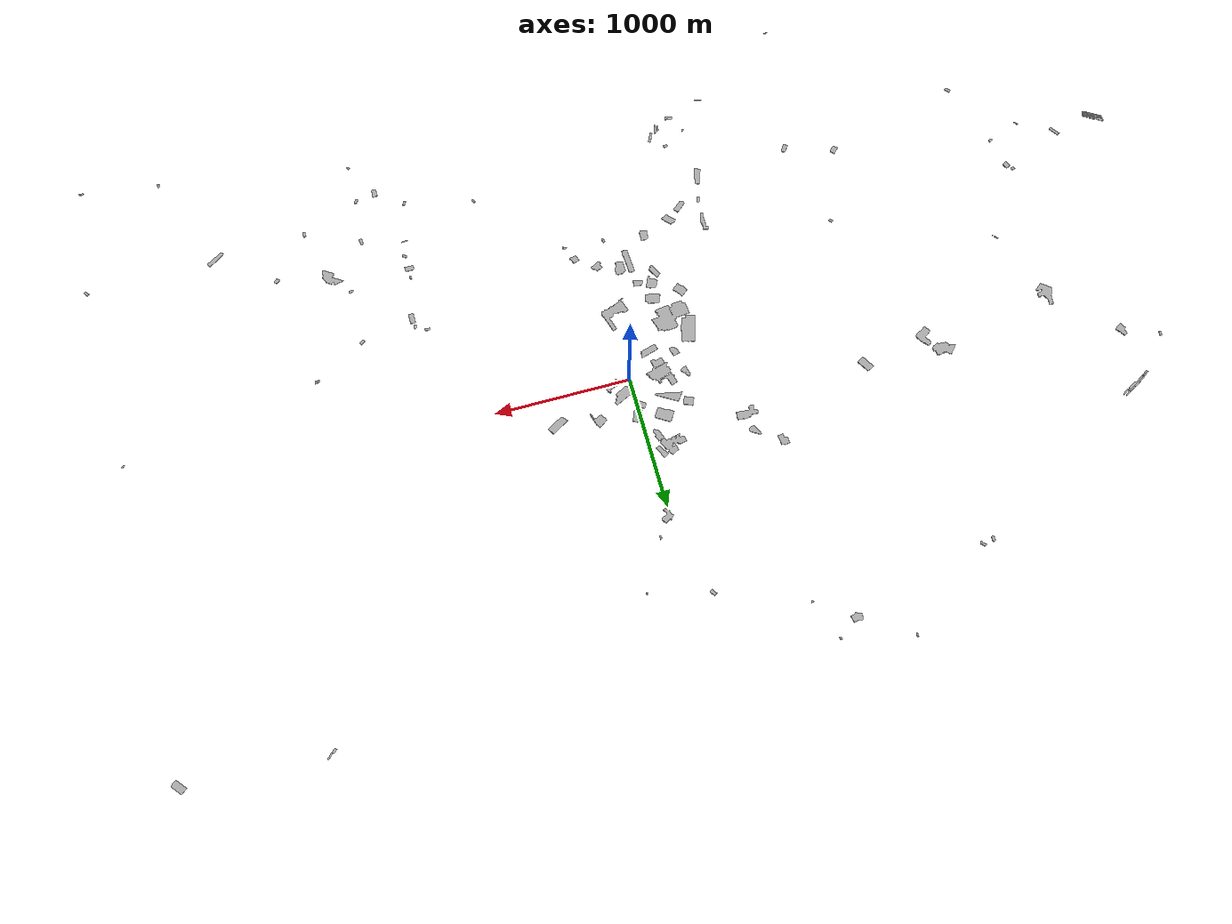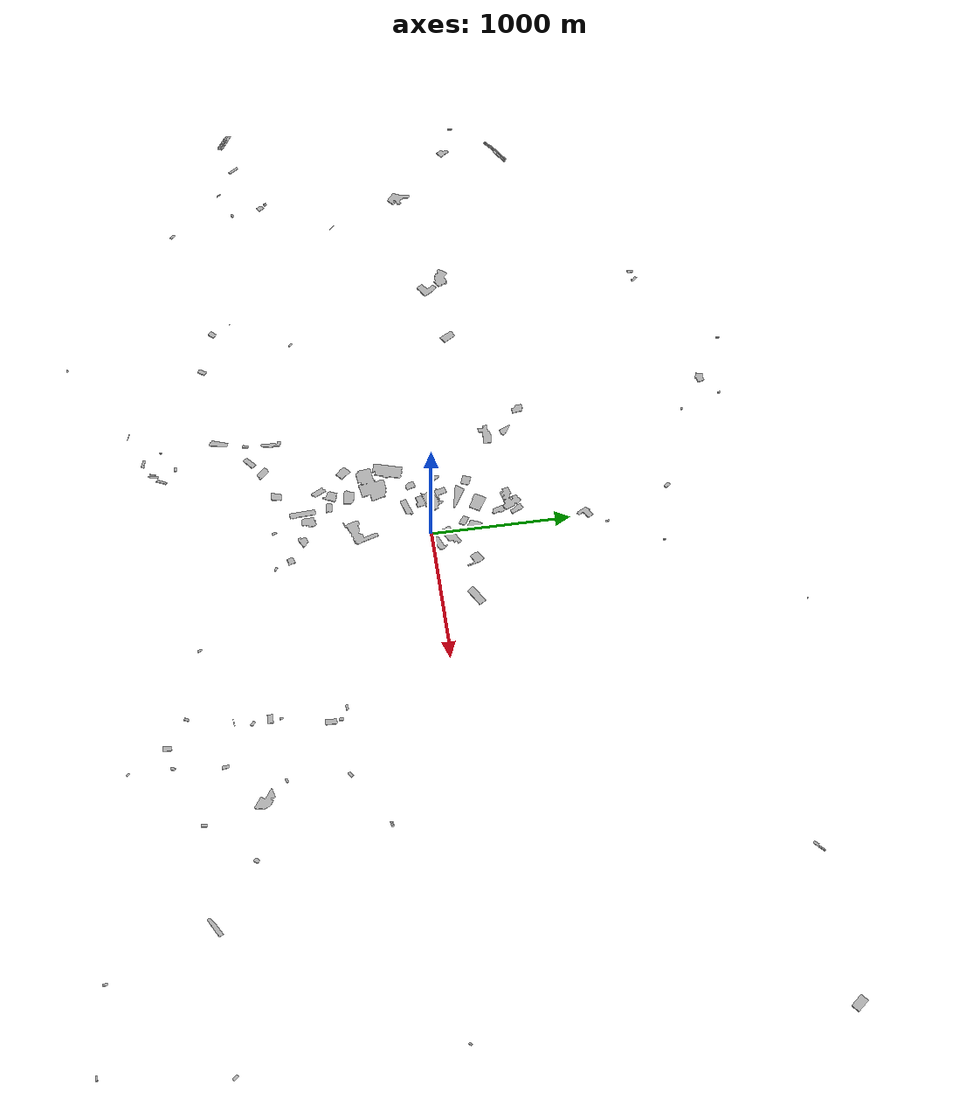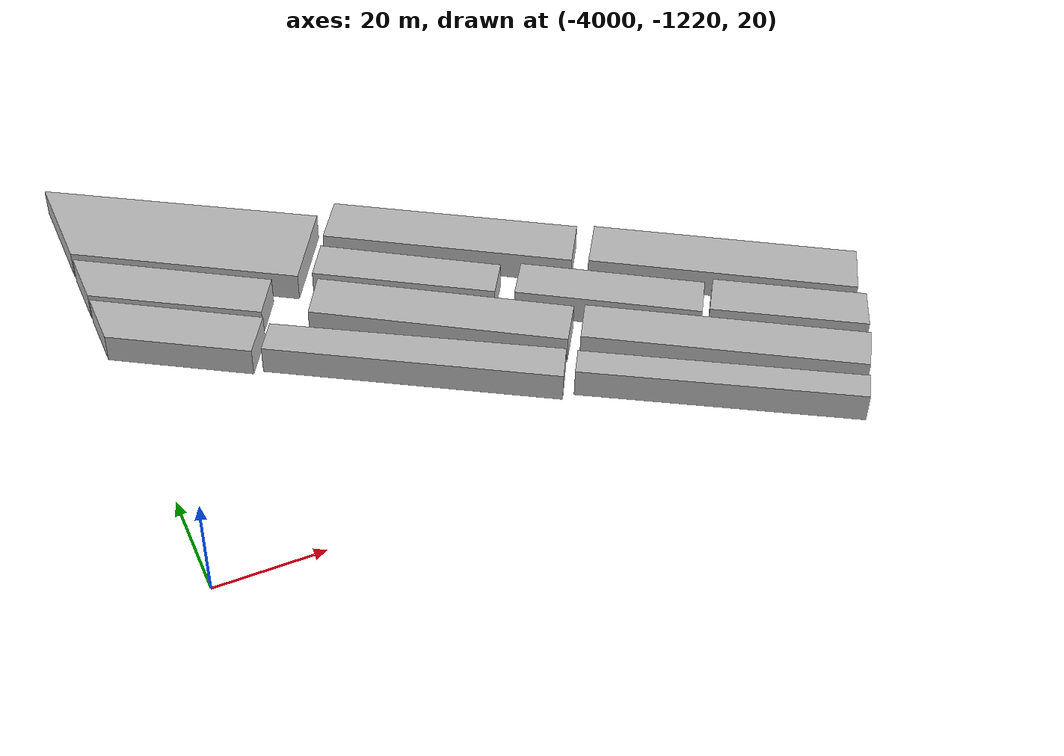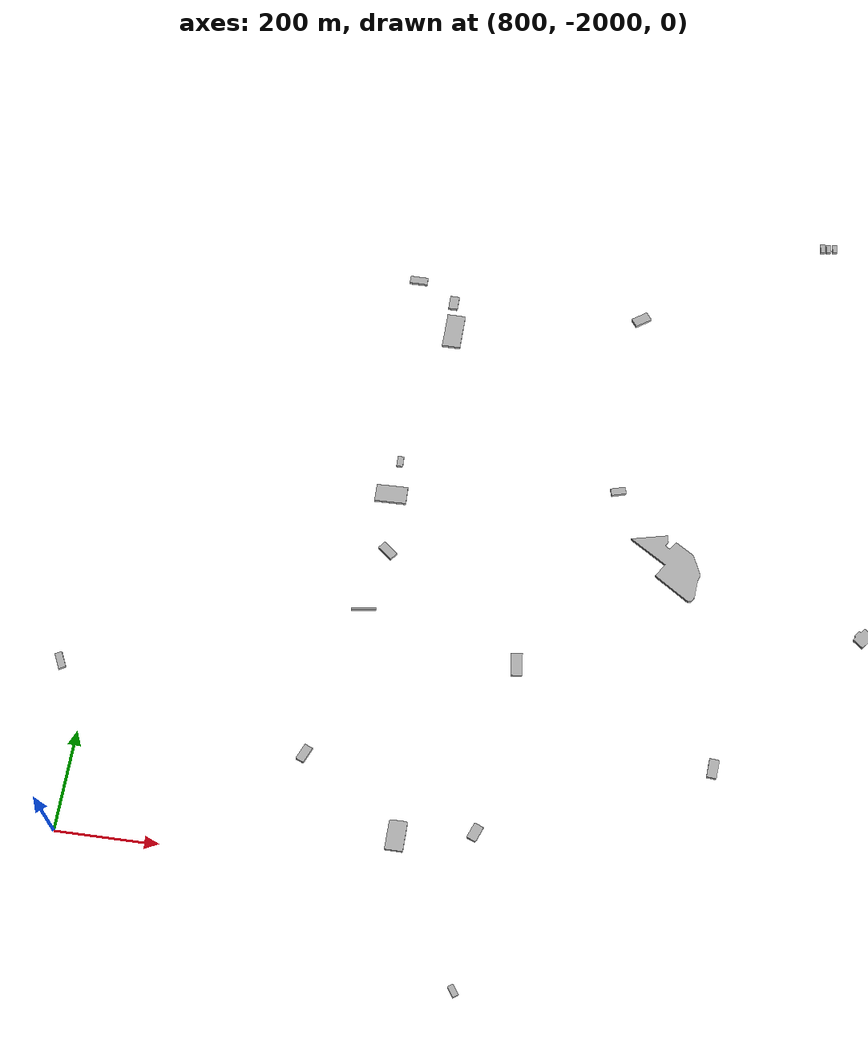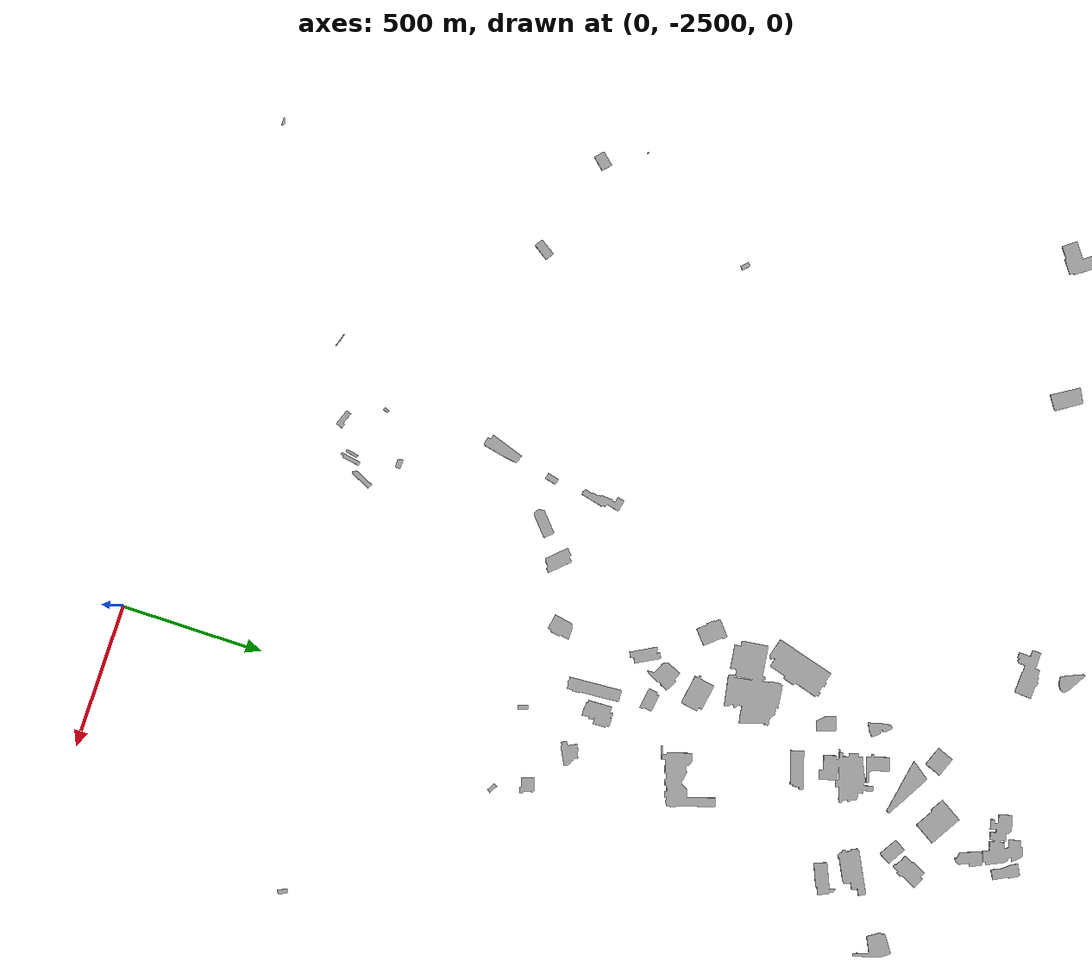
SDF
<sdf version="1.7">
 <world name="all_buildings_flat_prisms">
  <gravity>0 0 -9.8</gravity>
  <magnetic_field>6e-06 2.3e-05 -4.2e-05</magnetic_field>
  <atmosphere type="adiabatic"/>
  <scene>
   <ambient>0.65 0.65 0.65 1</ambient>
   <background>0.7 0.82 1 1</background>
   <shadows>false</shadows>
  </scene>
  <light name="sun" type="directional">
   <cast_shadows>false</cast_shadows>
   <pose>0 0 1000 0 0 0</pose>
   <diffuse>0.8 0.8 0.8 1</diffuse>
   <specular>0.2 0.2 0.2 1</specular>
   <direction>-0.5 0.2 -1</direction>
  </light>
  <include>
   <name>building_0000_assumed_a_apeadeiro_em_caminho_de_ferro</name>
   <uri>model://building_0000_assumed_a_apeadeiro_em_caminho_de_ferro</uri>
   <pose>-2900.528850 -394.488600 22.944476 0 0 0</pose>
  </include>
  <include>
   <name>building_0001_assumed_a_apeadeiro_em_caminho_de_ferro</name>
   <uri>model://building_0001_assumed_a_apeadeiro_em_caminho_de_ferro</uri>
   <pose>316.314150 1605.018900 79.373376 0 0 0</pose>
  </include>
  <include>
   <name>building_0002_assumed_a_apeadeiro_em_caminho_de_ferro</name>
   <uri>model://building_0002_assumed_a_apeadeiro_em_caminho_de_ferro</uri>
   <pose>-2042.072850 -1263.891600 15.009976 0 0 0</pose>
  </include>
  <include>
   <name>building_0003_assumed_a_apeadeiro_em_caminho_de_ferro</name>
   <uri>model://building_0003_assumed_a_apeadeiro_em_caminho_de_ferro</uri>
   <pose>-1098.286350 -2074.112100 15.259476 0 0 0</pose>
  </include>
  <include>
   <name>building_0004_assumed_a_apeadeiro_em_caminho_de_ferro</name>
   <uri>model://building_0004_assumed_a_apeadeiro_em_caminho_de_ferro</uri>
   <pose>908.125650 2480.673900 73.829376 0 0 0</pose>
  </include>
  <include>
   <name>building_0005_assumed_a_cais_de_acesso_ferroviario</name>
   <uri>model://building_0005_assumed_a_cais_de_acesso_ferroviario</uri>
   <pose>-2900.120350 -394.117100 20.018476 0 0 0</pose>
  </include>
  <include>
   <name>building_0006_assumed_a_cais_de_acesso_ferroviario</name>
   <uri>model://building_0006_assumed_a_cais_de_acesso_ferroviario</uri>
   <pose>-1098.375850 -2075.056100 12.438228 0 0 0</pose>
  </include>
  <include>
   <name>building_0007_assumed_a_cais_de_acesso_ferroviario</name>
   <uri>model://building_0007_assumed_a_cais_de_acesso_ferroviario</uri>
   <pose>1311.261650 -1489.805600 34.497156 0 0 0</pose>
  </include>
  <include>
   <name>building_0008_assumed_a_campo_de_jogos</name>
   <uri>model://building_0008_assumed_a_campo_de_jogos</uri>
   <pose>2188.046650 -544.059600 70.049977 0 0 0</pose>
  </include>
  <include>
   <name>building_0009_assumed_a_campo_de_jogos</name>
   <uri>model://building_0009_assumed_a_campo_de_jogos</uri>
   <pose>745.407150 -1676.292600 39.021121 0 0 0</pose>
  </include>
  <include>
   <name>building_0010_assumed_a_campo_de_jogos</name>
   <uri>model://building_0010_assumed_a_campo_de_jogos</uri>
   <pose>2162.720650 -546.484100 70.049977 0 0 0</pose>
  </include>
  <include>
   <name>building_0011_assumed_a_campo_de_jogos</name>
   <uri>model://building_0011_assumed_a_campo_de_jogos</uri>
   <pose>2014.192150 -1732.571100 40.027903 0 0 0</pose>
  </include>
  <include>
   <name>building_0012_assumed_a_campo_de_jogos</name>
   <uri>model://building_0012_assumed_a_campo_de_jogos</uri>
   <pose>3635.801650 -258.780600 100.049977 0 0 0</pose>
  </include>
  <include>
   <name>building_0013_assumed_a_campo_de_jogos</name>
   <uri>model://building_0013_assumed_a_campo_de_jogos</uri>
   <pose>2973.896650 -2398.116600 61.060538 0 0 0</pose>
  </include>
  <include>
   <name>building_0014_assumed_a_campo_de_jogos</name>
   <uri>model://building_0014_assumed_a_campo_de_jogos</uri>
   <pose>2174.886650 -545.392100 70.049977 0 0 0</pose>
  </include>
  <include>
   <name>building_0015_assumed_a_campo_de_jogos</name>
   <uri>model://building_0015_assumed_a_campo_de_jogos</uri>
   <pose>-3121.153850 -1161.085600 30.216676 0 0 0</pose>
  </include>
  <include>
   <name>building_0016_assumed_a_campo_de_jogos</name>
   <uri>model://building_0016_assumed_a_campo_de_jogos</uri>
   <pose>-861.705350 -1235.887600 71.547375 0 0 0</pose>
  </include>
  <include>
   <name>building_0017_assumed_a_campo_de_jogos</name>
   <uri>model://building_0017_assumed_a_campo_de_jogos</uri>
   <pose>-2933.140350 -1637.960600 63.891976 0 0 0</pose>
  </include>
  <include>
   <name>building_0018_assumed_a_campo_de_jogos</name>
   <uri>model://building_0018_assumed_a_campo_de_jogos</uri>
   <pose>-1764.043850 -826.878600 43.143763 0 0 0</pose>
  </include>
  <include>
   <name>building_0019_assumed_a_campo_de_jogos</name>
   <uri>model://building_0019_assumed_a_campo_de_jogos</uri>
   <pose>-1659.796350 350.923900 76.085653 0 0 0</pose>
  </include>
  <include>
   <name>building_0020_assumed_a_campo_de_jogos</name>
   <uri>model://building_0020_assumed_a_campo_de_jogos</uri>
   <pose>1316.623150 -739.139100 71.140151 0 0 0</pose>
  </include>
  <include>
   <name>building_0021_assumed_a_campo_de_jogos</name>
   <uri>model://building_0021_assumed_a_campo_de_jogos</uri>
   <pose>1397.370650 -784.489100 69.772976 0 0 0</pose>
  </include>
  <include>
   <name>building_0022_assumed_a_campo_de_jogos</name>
   <uri>model://building_0022_assumed_a_campo_de_jogos</uri>
   <pose>1331.809150 -1249.402600 68.021102 0 0 0</pose>
  </include>
  <include>
   <name>building_0023_assumed_a_campo_de_jogos</name>
   <uri>model://building_0023_assumed_a_campo_de_jogos</uri>
   <pose>1341.024650 -1365.241100 47.464296 0 0 0</pose>
  </include>
  <include>
   <name>building_0024_assumed_a_campo_de_jogos</name>
   <uri>model://building_0024_assumed_a_campo_de_jogos</uri>
   <pose>1243.958150 -1798.841100 29.356296 0 0 0</pose>
  </include>
  <include>
   <name>building_0025_assumed_a_campo_de_jogos</name>
   <uri>model://building_0025_assumed_a_campo_de_jogos</uri>
   <pose>1584.741650 -1908.817600 24.081483 0 0 0</pose>
  </include>
  <include>
   <name>building_0026_assumed_a_campo_de_jogos</name>
   <uri>model://building_0026_assumed_a_campo_de_jogos</uri>
   <pose>1622.779650 -1568.687600 34.558656 0 0 0</pose>
  </include>
  <include>
   <name>building_0027_assumed_a_campo_de_jogos</name>
   <uri>model://building_0027_assumed_a_campo_de_jogos</uri>
   <pose>3703.814150 2095.172400 98.993593 0 0 0</pose>
  </include>
  <include>
   <name>building_0028_assumed_a_campo_de_jogos</name>
   <uri>model://building_0028_assumed_a_campo_de_jogos</uri>
   <pose>-2129.399850 1840.569900 43.401613 0 0 0</pose>
  </include>
  <include>
   <name>building_0029_assumed_a_campo_de_jogos</name>
   <uri>model://building_0029_assumed_a_campo_de_jogos</uri>
   <pose>1406.072150 -853.652100 69.279398 0 0 0</pose>
  </include>
  <include>
   <name>building_0030_assumed_a_campo_de_jogos</name>
   <uri>model://building_0030_assumed_a_campo_de_jogos</uri>
   <pose>-880.168850 2259.308400 76.944676 0 0 0</pose>
  </include>
  <include>
   <name>building_0031_assumed_a_campo_de_jogos</name>
   <uri>model://building_0031_assumed_a_campo_de_jogos</uri>
   <pose>-1967.912350 -1403.408100 9.611776 0 0 0</pose>
  </include>
  <include>
   <name>building_0032_assumed_a_campo_de_jogos</name>
   <uri>model://building_0032_assumed_a_campo_de_jogos</uri>
   <pose>1581.718150 -2202.429600 10.455376 0 0 0</pose>
  </include>
  <include>
   <name>building_0033_assumed_a_campo_de_jogos</name>
   <uri>model://building_0033_assumed_a_campo_de_jogos</uri>
   <pose>-3792.918350 672.457900 59.116276 0 0 0</pose>
  </include>
  <include>
   <name>building_0034_assumed_a_campo_de_jogos</name>
   <uri>model://building_0034_assumed_a_campo_de_jogos</uri>
   <pose>-914.440850 -1848.110100 29.936276 0 0 0</pose>
  </include>
  <include>
   <name>building_0035_assumed_a_campo_de_jogos</name>
   <uri>model://building_0035_assumed_a_campo_de_jogos</uri>
   <pose>-128.044850 1715.476900 75.916929 0 0 0</pose>
  </include>
  <include>
   <name>building_0036_assumed_a_campo_de_jogos</name>
   <uri>model://building_0036_assumed_a_campo_de_jogos</uri>
   <pose>196.453650 -1109.476100 72.050576 0 0 0</pose>
  </include>
  <include>
   <name>building_0037_assumed_a_campo_de_jogos</name>
   <uri>model://building_0037_assumed_a_campo_de_jogos</uri>
   <pose>1782.677150 -1181.955600 63.277695 0 0 0</pose>
  </include>
  <include>
   <name>building_0038_assumed_a_campo_de_jogos</name>
   <uri>model://building_0038_assumed_a_campo_de_jogos</uri>
   <pose>1793.688650 -767.808100 58.996575 0 0 0</pose>
  </include>
  <include>
   <name>building_0039_assumed_a_campo_de_jogos</name>
   <uri>model://building_0039_assumed_a_campo_de_jogos</uri>
   <pose>3537.623150 -2468.379100 78.151692 0 0 0</pose>
  </include>
  <include>
   <name>building_0040_assumed_a_campo_de_jogos</name>
   <uri>model://building_0040_assumed_a_campo_de_jogos</uri>
   <pose>3644.484650 -1656.024600 85.412076 0 0 0</pose>
  </include>
  <include>
   <name>building_0041_assumed_a_campo_de_jogos</name>
   <uri>model://building_0041_assumed_a_campo_de_jogos</uri>
   <pose>1339.216650 -1174.450100 69.119977 0 0 0</pose>
  </include>
  <include>
   <name>building_0042_assumed_a_campo_de_jogos</name>
   <uri>model://building_0042_assumed_a_campo_de_jogos</uri>
   <pose>116.688150 1236.140900 83.274863 0 0 0</pose>
  </include>
  <include>
   <name>building_0043_assumed_a_campo_de_jogos</name>
   <uri>model://building_0043_assumed_a_campo_de_jogos</uri>
   <pose>-94.146350 -1093.125600 75.045979 0 0 0</pose>
  </include>
  <include>
   <name>building_0044_assumed_a_cemiterio</name>
   <uri>model://building_0044_assumed_a_cemiterio</uri>
   <pose>-2052.262850 1858.563400 46.372251 0 0 0</pose>
  </include>
  <include>
   <name>building_0045_assumed_a_cemiterio</name>
   <uri>model://building_0045_assumed_a_cemiterio</uri>
   <pose>-1034.242850 2142.386900 77.216977 0 0 0</pose>
  </include>
  <include>
   <name>building_0046_assumed_a_cemiterio</name>
   <uri>model://building_0046_assumed_a_cemiterio</uri>
   <pose>-1759.982150 -2494.533300 19.706316 0 0 0</pose>
  </include>
  <include>
   <name>building_0047_assumed_a_cemiterio</name>
   <uri>model://building_0047_assumed_a_cemiterio</uri>
   <pose>-1608.840850 -1502.434600 26.723677 0 0 0</pose>
  </include>
  <include>
   <name>building_0048_assumed_a_cemiterio</name>
   <uri>model://building_0048_assumed_a_cemiterio</uri>
   <pose>1440.112150 -1936.520600 32.642035 0 0 0</pose>
  </include>
  <include>
   <name>building_0049_assumed_a_cemiterio</name>
   <uri>model://building_0049_assumed_a_cemiterio</uri>
   <pose>1888.699650 -1335.180600 59.038976 0 0 0</pose>
  </include>
  <include>
   <name>building_0050_assumed_a_cemiterio</name>
   <uri>model://building_0050_assumed_a_cemiterio</uri>
   <pose>2688.521150 -1713.507600 21.286576 0 0 0</pose>
  </include>
  <include>
   <name>building_0051_assumed_a_cemiterio</name>
   <uri>model://building_0051_assumed_a_cemiterio</uri>
   <pose>-3526.363850 575.881900 65.066881 0 0 0</pose>
  </include>
  <include>
   <name>building_0052_assumed_a_cemiterio</name>
   <uri>model://building_0052_assumed_a_cemiterio</uri>
   <pose>-3168.768850 -935.200100 25.504483 0 0 0</pose>
  </include>
  <include>
   <name>building_0053_assumed_a_cemiterio</name>
   <uri>model://building_0053_assumed_a_cemiterio</uri>
   <pose>-3208.302350 -893.675100 25.722330 0 0 0</pose>
  </include>
  <include>
   <name>building_0054_assumed_a_estufa</name>
   <uri>model://building_0054_assumed_a_estufa</uri>
   <pose>2288.906650 -1422.959600 26.318018 0 0 0</pose>
  </include>
  <include>
   <name>building_0055_assumed_a_central_electrica</name>
   <uri>model://building_0055_assumed_a_central_electrica</uri>
   <pose>-231.206850 228.826400 80.687603 0 0 0</pose>
  </include>
  <include>
   <name>building_0056_assumed_a_estufa</name>
   <uri>model://building_0056_assumed_a_estufa</uri>
   <pose>-3352.280350 -1252.235600 24.254544 0 0 0</pose>
  </include>
  <include>
   <name>building_0057_assumed_a_estufa</name>
   <uri>model://building_0057_assumed_a_estufa</uri>
   <pose>-3985.295400 -1152.783850 10.135823 0 0 0</pose>
  </include>
  <include>
   <name>building_0058_assumed_a_subestacao</name>
   <uri>model://building_0058_assumed_a_subestacao</uri>
   <pose>595.182650 235.429900 85.762822 0 0 0</pose>
  </include>
  <include>
   <name>building_0059_assumed_a_estufa</name>
   <uri>model://building_0059_assumed_a_estufa</uri>
   <pose>-3582.158850 947.099900 69.828965 0 0 0</pose>
  </include>
  <include>
   <name>building_0060_assumed_a_grande_construcao</name>
   <uri>model://building_0060_assumed_a_grande_construcao</uri>
   <pose>-15.759850 236.109400 89.906576 0 0 0</pose>
  </include>
  <include>
   <name>building_0061_assumed_a_estufa</name>
   <uri>model://building_0061_assumed_a_estufa</uri>
   <pose>-3898.250350 -1207.836100 11.869576 0 0 0</pose>
  </include>
  <include>
   <name>building_0062_assumed_a_estufa</name>
   <uri>model://building_0062_assumed_a_estufa</uri>
   <pose>-3892.449850 -1198.838100 11.825234 0 0 0</pose>
  </include>
  <include>
   <name>building_0063_assumed_a_estufa</name>
   <uri>model://building_0063_assumed_a_estufa</uri>
   <pose>-3938.810350 -1170.386600 11.393537 0 0 0</pose>
  </include>
  <include>
   <name>building_0064_assumed_a_estufa</name>
   <uri>model://building_0064_assumed_a_estufa</uri>
   <pose>-3947.665350 -1178.625100 11.057108 0 0 0</pose>
  </include>
  <include>
   <name>building_0065_assumed_a_estufa</name>
   <uri>model://building_0065_assumed_a_estufa</uri>
   <pose>-3906.445850 -1178.232100 11.720076 0 0 0</pose>
  </include>
  <include>
   <name>building_0066_assumed_a_estufa</name>
   <uri>model://building_0066_assumed_a_estufa</uri>
   <pose>-3877.134850 -1196.198600 12.295076 0 0 0</pose>
  </include>
  <include>
   <name>building_0067_assumed_a_estufa</name>
   <uri>model://building_0067_assumed_a_estufa</uri>
   <pose>-3881.882350 -1179.162600 11.927076 0 0 0</pose>
  </include>
  <include>
   <name>building_0068_assumed_a_estufa</name>
   <uri>model://building_0068_assumed_a_estufa</uri>
   <pose>-3928.206850 -1150.226100 11.517369 0 0 0</pose>
  </include>
  <include>
   <name>building_0069_assumed_a_estufa</name>
   <uri>model://building_0069_assumed_a_estufa</uri>
   <pose>-3940.538850 -1156.974100 11.389505 0 0 0</pose>
  </include>
  <include>
   <name>building_0070_assumed_a_estufa</name>
   <uri>model://building_0070_assumed_a_estufa</uri>
   <pose>-3611.081350 -1116.402600 18.512576 0 0 0</pose>
  </include>
  <include>
   <name>building_0071_assumed_a_estufa</name>
   <uri>model://building_0071_assumed_a_estufa</uri>
   <pose>-3576.565350 938.795900 69.802576 0 0 0</pose>
  </include>
  <include>
   <name>building_0072_assumed_a_estufa</name>
   <uri>model://building_0072_assumed_a_estufa</uri>
   <pose>-3485.475350 997.168400 70.690576 0 0 0</pose>
  </include>
  <include>
   <name>building_0073_assumed_a_estufa</name>
   <uri>model://building_0073_assumed_a_estufa</uri>
   <pose>-3538.322350 980.011400 71.098576 0 0 0</pose>
  </include>
  <include>
   <name>building_0074_assumed_a_estufa</name>
   <uri>model://building_0074_assumed_a_estufa</uri>
   <pose>-3493.958850 1008.587900 71.780870 0 0 0</pose>
  </include>
  <include>
   <name>building_0075_assumed_a_estufa</name>
   <uri>model://building_0075_assumed_a_estufa</uri>
   <pose>-3445.892350 1035.721400 72.574576 0 0 0</pose>
  </include>
  <include>
   <name>building_0076_assumed_a_estufa</name>
   <uri>model://building_0076_assumed_a_estufa</uri>
   <pose>-3404.613350 1060.030900 72.502038 0 0 0</pose>
  </include>
  <include>
   <name>building_0077_assumed_a_estufa</name>
   <uri>model://building_0077_assumed_a_estufa</uri>
   <pose>-3391.848850 1045.617400 72.561586 0 0 0</pose>
  </include>
  <include>
   <name>building_0078_assumed_a_estufa</name>
   <uri>model://building_0078_assumed_a_estufa</uri>
   <pose>-1399.723350 2368.459900 54.658976 0 0 0</pose>
  </include>
  <include>
   <name>building_0079_assumed_a_estufa</name>
   <uri>model://building_0079_assumed_a_estufa</uri>
   <pose>-841.042350 -1978.869100 22.641976 0 0 0</pose>
  </include>
  <include>
   <name>building_0080_assumed_a_estufa</name>
   <uri>model://building_0080_assumed_a_estufa</uri>
   <pose>-753.537350 -1749.249600 37.147976 0 0 0</pose>
  </include>
  <include>
   <name>building_0081_assumed_a_estufa</name>
   <uri>model://building_0081_assumed_a_estufa</uri>
   <pose>-664.172350 -1855.965600 27.289576 0 0 0</pose>
  </include>
  <include>
   <name>building_0082_assumed_a_estufa</name>
   <uri>model://building_0082_assumed_a_estufa</uri>
   <pose>-717.609850 -1914.148600 24.551622 0 0 0</pose>
  </include>
  <include>
   <name>building_0083_assumed_a_estufa</name>
   <uri>model://building_0083_assumed_a_estufa</uri>
   <pose>-737.912850 -1914.903100 24.570346 0 0 0</pose>
  </include>
  <include>
   <name>building_0084_assumed_a_grande_construcao</name>
   <uri>model://building_0084_assumed_a_grande_construcao</uri>
   <pose>-909.490350 -1425.796600 77.768976 0 0 0</pose>
  </include>
  <include>
   <name>building_0085_assumed_a_estufa</name>
   <uri>model://building_0085_assumed_a_estufa</uri>
   <pose>2647.541150 2106.769900 30.674304 0 0 0</pose>
  </include>
  <include>
   <name>building_0086_assumed_a_estufa</name>
   <uri>model://building_0086_assumed_a_estufa</uri>
   <pose>2684.003150 2135.692400 31.282861 0 0 0</pose>
  </include>
  <include>
   <name>building_0087_assumed_a_estufa</name>
   <uri>model://building_0087_assumed_a_estufa</uri>
   <pose>-3975.394350 -1126.645600 10.474663 0 0 0</pose>
  </include>
  <include>
   <name>building_0088_assumed_a_estufa</name>
   <uri>model://building_0088_assumed_a_estufa</uri>
   <pose>-3982.779350 -1141.623500 10.223376 0 0 0</pose>
  </include>
  <include>
   <name>building_0089_assumed_a_grande_construcao</name>
   <uri>model://building_0089_assumed_a_grande_construcao</uri>
   <pose>-707.755350 -1215.504600 78.358886 0 0 0</pose>
  </include>
  <include>
   <name>building_0090_assumed_a_grande_construcao</name>
   <uri>model://building_0090_assumed_a_grande_construcao</uri>
   <pose>-225.230350 -883.177100 79.377195 0 0 0</pose>
  </include>
  <include>
   <name>building_0091_assumed_a_grande_construcao</name>
   <uri>model://building_0091_assumed_a_grande_construcao</uri>
   <pose>-3094.148850 160.356900 64.920699 0 0 0</pose>
  </include>
  <include>
   <name>building_0092_assumed_a_grande_construcao</name>
   <uri>model://building_0092_assumed_a_grande_construcao</uri>
   <pose>-2247.530850 378.753400 65.605976 0 0 0</pose>
  </include>
  <include>
   <name>building_0093_assumed_a_grande_construcao</name>
   <uri>model://building_0093_assumed_a_grande_construcao</uri>
   <pose>-2130.438350 258.254400 76.849976 0 0 0</pose>
  </include>
  <include>
   <name>building_0094_assumed_a_casa</name>
   <uri>model://building_0094_assumed_a_casa</uri>
   <pose>-769.847350 1957.449400 76.976624 0 0 0</pose>
  </include>
  <include>
   <name>building_0095_assumed_a_grande_construcao</name>
   <uri>model://building_0095_assumed_a_grande_construcao</uri>
   <pose>-846.687850 -1051.025100 79.850857 0 0 0</pose>
  </include>
  <include>
   <name>building_0096_assumed_a_grande_construcao</name>
   <uri>model://building_0096_assumed_a_grande_construcao</uri>
   <pose>-357.651850 -100.455600 89.429576 0 0 0</pose>
  </include>
  <include>
   <name>building_0097_assumed_a_grande_construcao</name>
   <uri>model://building_0097_assumed_a_grande_construcao</uri>
   <pose>-728.180350 492.207400 87.667344 0 0 0</pose>
  </include>
  <include>
   <name>building_0098_assumed_a_grande_construcao</name>
   <uri>model://building_0098_assumed_a_grande_construcao</uri>
   <pose>-742.973350 642.435900 92.014380 0 0 0</pose>
  </include>
  <include>
   <name>building_0099_assumed_a_grande_construcao</name>
   <uri>model://building_0099_assumed_a_grande_construcao</uri>
   <pose>-921.942350 758.913400 91.530326 0 0 0</pose>
  </include>
  <include>
   <name>building_0100_assumed_a_grande_construcao</name>
   <uri>model://building_0100_assumed_a_grande_construcao</uri>
   <pose>-505.414350 -245.196100 87.749736 0 0 0</pose>
  </include>
  <include>
   <name>building_0101_assumed_a_grande_construcao</name>
   <uri>model://building_0101_assumed_a_grande_construcao</uri>
   <pose>-407.239850 -373.944100 81.554002 0 0 0</pose>
  </include>
  <include>
   <name>building_0102_assumed_a_grande_construcao</name>
   <uri>model://building_0102_assumed_a_grande_construcao</uri>
   <pose>-530.991350 -560.903600 81.375932 0 0 0</pose>
  </include>
  <include>
   <name>building_0103_assumed_a_grande_construcao</name>
   <uri>model://building_0103_assumed_a_grande_construcao</uri>
   <pose>-603.337850 -1130.708100 82.377576 0 0 0</pose>
  </include>
  <include>
   <name>building_0104_assumed_a_grande_construcao</name>
   <uri>model://building_0104_assumed_a_grande_construcao</uri>
   <pose>-392.926350 -1055.063600 84.854458 0 0 0</pose>
  </include>
  <include>
   <name>building_0105_assumed_a_grande_construcao</name>
   <uri>model://building_0105_assumed_a_grande_construcao</uri>
   <pose>-389.643350 -753.751600 82.163996 0 0 0</pose>
  </include>
  <include>
   <name>building_0106_assumed_a_grande_construcao</name>
   <uri>model://building_0106_assumed_a_grande_construcao</uri>
   <pose>304.517150 270.133400 89.070348 0 0 0</pose>
  </include>
  <include>
   <name>building_0107_assumed_a_grande_construcao</name>
   <uri>model://building_0107_assumed_a_grande_construcao</uri>
   <pose>-343.337350 -677.281100 81.696019 0 0 0</pose>
  </include>
  <include>
   <name>building_0108_assumed_a_grande_construcao</name>
   <uri>model://building_0108_assumed_a_grande_construcao</uri>
   <pose>-250.346850 -692.842100 83.303543 0 0 0</pose>
  </include>
  <include>
   <name>building_0109_assumed_a_grande_construcao</name>
   <uri>model://building_0109_assumed_a_grande_construcao</uri>
   <pose>-321.086850 -544.838600 83.284547 0 0 0</pose>
  </include>
  <include>
   <name>building_0110_assumed_a_grande_construcao</name>
   <uri>model://building_0110_assumed_a_grande_construcao</uri>
   <pose>85.155150 130.656900 80.937264 0 0 0</pose>
  </include>
  <include>
   <name>building_0111_assumed_a_grande_construcao</name>
   <uri>model://building_0111_assumed_a_grande_construcao</uri>
   <pose>-205.287350 18.063400 84.674576 0 0 0</pose>
  </include>
  <include>
   <name>building_0112_assumed_a_grande_construcao</name>
   <uri>model://building_0112_assumed_a_grande_construcao</uri>
   <pose>-261.587350 104.160400 85.176837 0 0 0</pose>
  </include>
  <include>
   <name>building_0113_assumed_a_grande_construcao</name>
   <uri>model://building_0113_assumed_a_grande_construcao</uri>
   <pose>-391.043850 72.575400 87.380576 0 0 0</pose>
  </include>
  <include>
   <name>building_0114_assumed_a_grande_construcao</name>
   <uri>model://building_0114_assumed_a_grande_construcao</uri>
   <pose>-351.368350 298.019400 88.472576 0 0 0</pose>
  </include>
  <include>
   <name>building_0115_assumed_a_grande_construcao</name>
   <uri>model://building_0115_assumed_a_grande_construcao</uri>
   <pose>29.912150 307.312900 87.831846 0 0 0</pose>
  </include>
  <include>
   <name>building_0116_assumed_a_grande_construcao</name>
   <uri>model://building_0116_assumed_a_grande_construcao</uri>
   <pose>-182.345350 -149.930100 87.757897 0 0 0</pose>
  </include>
  <include>
   <name>building_0117_assumed_a_grande_construcao</name>
   <uri>model://building_0117_assumed_a_grande_construcao</uri>
   <pose>-25.252350 -491.401600 77.744760 0 0 0</pose>
  </include>
  <include>
   <name>building_0118_assumed_a_grande_construcao</name>
   <uri>model://building_0118_assumed_a_grande_construcao</uri>
   <pose>-157.901850 353.983400 86.365576 0 0 0</pose>
  </include>
  <include>
   <name>building_0119_assumed_a_grande_construcao</name>
   <uri>model://building_0119_assumed_a_grande_construcao</uri>
   <pose>7.979650 -899.734600 80.212576 0 0 0</pose>
  </include>
  <include>
   <name>building_0120_assumed_a_grande_construcao</name>
   <uri>model://building_0120_assumed_a_grande_construcao</uri>
   <pose>-151.424850 -846.829100 77.659576 0 0 0</pose>
  </include>
  <include>
   <name>building_0121_assumed_a_grande_construcao</name>
   <uri>model://building_0121_assumed_a_grande_construcao</uri>
   <pose>149.864150 -999.359600 76.295643 0 0 0</pose>
  </include>
  <include>
   <name>building_0122_assumed_a_grande_construcao</name>
   <uri>model://building_0122_assumed_a_grande_construcao</uri>
   <pose>142.171650 45.152400 81.517266 0 0 0</pose>
  </include>
  <include>
   <name>building_0123_assumed_a_grande_construcao</name>
   <uri>model://building_0123_assumed_a_grande_construcao</uri>
   <pose>-163.340850 590.390400 83.551576 0 0 0</pose>
  </include>
  <include>
   <name>building_0124_assumed_a_grande_construcao</name>
   <uri>model://building_0124_assumed_a_grande_construcao</uri>
   <pose>28.809650 1091.031900 86.754926 0 0 0</pose>
  </include>
  <include>
   <name>building_0125_assumed_a_grande_construcao</name>
   <uri>model://building_0125_assumed_a_grande_construcao</uri>
   <pose>-68.057350 619.154400 84.589752 0 0 0</pose>
  </include>
  <include>
   <name>building_0126_assumed_a_grande_construcao</name>
   <uri>model://building_0126_assumed_a_grande_construcao</uri>
   <pose>-75.638850 490.683900 87.837382 0 0 0</pose>
  </include>
 </world>
</sdf>

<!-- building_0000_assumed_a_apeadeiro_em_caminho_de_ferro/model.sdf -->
<sdf version="1.7">
  <model name="building_0000_assumed_a_apeadeiro_em_caminho_de_ferro">
    <static>true</static>
    <link name="building_link">
      <visual name="building_visual">
        <geometry>
          <mesh>
            <uri>model://building_0000_assumed_a_apeadeiro_em_caminho_de_ferro/meshes/construction_0000_assumed_A_Apeadeiro_em_caminho_de_ferro_h6m.obj</uri>
          </mesh>
        </geometry>
      </visual>
    <collision name="building_collision">
      <geometry>
        <mesh>
          <uri>model://building_0000_assumed_a_apeadeiro_em_caminho_de_ferro/meshes/construction_0000_assumed_A_Apeadeiro_em_caminho_de_ferro_h6m.obj</uri>
        </mesh>
      </geometry>
    </collision>
    </link>
  </model>
</sdf>

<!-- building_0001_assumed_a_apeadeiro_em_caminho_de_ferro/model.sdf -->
<sdf version="1.7">
  <model name="building_0001_assumed_a_apeadeiro_em_caminho_de_ferro">
    <static>true</static>
    <link name="building_link">
      <visual name="building_visual">
        <geometry>
          <mesh>
            <uri>model://building_0001_assumed_a_apeadeiro_em_caminho_de_ferro/meshes/construction_0001_assumed_A_Apeadeiro_em_caminho_de_ferro_h6m.obj</uri>
          </mesh>
        </geometry>
      </visual>
    <collision name="building_collision">
      <geometry>
        <mesh>
          <uri>model://building_0001_assumed_a_apeadeiro_em_caminho_de_ferro/meshes/construction_0001_assumed_A_Apeadeiro_em_caminho_de_ferro_h6m.obj</uri>
        </mesh>
      </geometry>
    </collision>
    </link>
  </model>
</sdf>

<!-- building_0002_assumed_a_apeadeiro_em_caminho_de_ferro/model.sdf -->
<sdf version="1.7">
  <model name="building_0002_assumed_a_apeadeiro_em_caminho_de_ferro">
    <static>true</static>
    <link name="building_link">
      <visual name="building_visual">
        <geometry>
          <mesh>
            <uri>model://building_0002_assumed_a_apeadeiro_em_caminho_de_ferro/meshes/construction_0002_assumed_A_Apeadeiro_em_caminho_de_ferro_h6m.obj</uri>
          </mesh>
        </geometry>
      </visual>
    <collision name="building_collision">
      <geometry>
        <mesh>
          <uri>model://building_0002_assumed_a_apeadeiro_em_caminho_de_ferro/meshes/construction_0002_assumed_A_Apeadeiro_em_caminho_de_ferro_h6m.obj</uri>
        </mesh>
      </geometry>
    </collision>
    </link>
  </model>
</sdf>

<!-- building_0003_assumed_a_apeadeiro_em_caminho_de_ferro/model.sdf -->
<sdf version="1.7">
  <model name="building_0003_assumed_a_apeadeiro_em_caminho_de_ferro">
    <static>true</static>
    <link name="building_link">
      <visual name="building_visual">
        <geometry>
          <mesh>
            <uri>model://building_0003_assumed_a_apeadeiro_em_caminho_de_ferro/meshes/construction_0003_assumed_A_Apeadeiro_em_caminho_de_ferro_h6m.obj</uri>
          </mesh>
        </geometry>
      </visual>
    <collision name="building_collision">
      <geometry>
        <mesh>
          <uri>model://building_0003_assumed_a_apeadeiro_em_caminho_de_ferro/meshes/construction_0003_assumed_A_Apeadeiro_em_caminho_de_ferro_h6m.obj</uri>
        </mesh>
      </geometry>
    </collision>
    </link>
  </model>
</sdf>

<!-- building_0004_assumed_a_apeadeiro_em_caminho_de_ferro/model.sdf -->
<sdf version="1.7">
  <model name="building_0004_assumed_a_apeadeiro_em_caminho_de_ferro">
    <static>true</static>
    <link name="building_link">
      <visual name="building_visual">
        <geometry>
          <mesh>
            <uri>model://building_0004_assumed_a_apeadeiro_em_caminho_de_ferro/meshes/construction_0004_assumed_A_Apeadeiro_em_caminho_de_ferro_h6m.obj</uri>
          </mesh>
        </geometry>
      </visual>
    <collision name="building_collision">
      <geometry>
        <mesh>
          <uri>model://building_0004_assumed_a_apeadeiro_em_caminho_de_ferro/meshes/construction_0004_assumed_A_Apeadeiro_em_caminho_de_ferro_h6m.obj</uri>
        </mesh>
      </geometry>
    </collision>
    </link>
  </model>
</sdf>

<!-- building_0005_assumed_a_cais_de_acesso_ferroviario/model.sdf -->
<sdf version="1.7">
  <model name="building_0005_assumed_a_cais_de_acesso_ferroviario">
    <static>true</static>
    <link name="building_link">
      <visual name="building_visual">
        <geometry>
          <mesh>
            <uri>model://building_0005_assumed_a_cais_de_acesso_ferroviario/meshes/construction_0005_assumed_A_Cais_de_acesso_ferroviario_h6m.obj</uri>
          </mesh>
        </geometry>
      </visual>
    <collision name="building_collision">
      <geometry>
        <mesh>
          <uri>model://building_0005_assumed_a_cais_de_acesso_ferroviario/meshes/construction_0005_assumed_A_Cais_de_acesso_ferroviario_h6m.obj</uri>
        </mesh>
      </geometry>
    </collision>
    </link>
  </model>
</sdf>

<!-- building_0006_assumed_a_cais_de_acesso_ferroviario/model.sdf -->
<sdf version="1.7">
  <model name="building_0006_assumed_a_cais_de_acesso_ferroviario">
    <static>true</static>
    <link name="building_link">
      <visual name="building_visual">
        <geometry>
          <mesh>
            <uri>model://building_0006_assumed_a_cais_de_acesso_ferroviario/meshes/construction_0006_assumed_A_Cais_de_acesso_ferroviario_h6m.obj</uri>
          </mesh>
        </geometry>
      </visual>
    <collision name="building_collision">
      <geometry>
        <mesh>
          <uri>model://building_0006_assumed_a_cais_de_acesso_ferroviario/meshes/construction_0006_assumed_A_Cais_de_acesso_ferroviario_h6m.obj</uri>
        </mesh>
      </geometry>
    </collision>
    </link>
  </model>
</sdf>

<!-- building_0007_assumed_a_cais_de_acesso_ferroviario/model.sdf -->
<sdf version="1.7">
  <model name="building_0007_assumed_a_cais_de_acesso_ferroviario">
    <static>true</static>
    <link name="building_link">
      <visual name="building_visual">
        <geometry>
          <mesh>
            <uri>model://building_0007_assumed_a_cais_de_acesso_ferroviario/meshes/construction_0007_assumed_A_Cais_de_acesso_ferroviario_h6m.obj</uri>
          </mesh>
        </geometry>
      </visual>
    <collision name="building_collision">
      <geometry>
        <mesh>
          <uri>model://building_0007_assumed_a_cais_de_acesso_ferroviario/meshes/construction_0007_assumed_A_Cais_de_acesso_ferroviario_h6m.obj</uri>
        </mesh>
      </geometry>
    </collision>
    </link>
  </model>
</sdf>

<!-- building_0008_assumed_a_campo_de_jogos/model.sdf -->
<sdf version="1.7">
  <model name="building_0008_assumed_a_campo_de_jogos">
    <static>true</static>
    <link name="building_link">
      <visual name="building_visual">
        <geometry>
          <mesh>
            <uri>model://building_0008_assumed_a_campo_de_jogos/meshes/construction_0008_assumed_A_Campo_de_jogos_h6m.obj</uri>
          </mesh>
        </geometry>
      </visual>
    <collision name="building_collision">
      <geometry>
        <mesh>
          <uri>model://building_0008_assumed_a_campo_de_jogos/meshes/construction_0008_assumed_A_Campo_de_jogos_h6m.obj</uri>
        </mesh>
      </geometry>
    </collision>
    </link>
  </model>
</sdf>

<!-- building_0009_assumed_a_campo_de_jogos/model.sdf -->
<sdf version="1.7">
  <model name="building_0009_assumed_a_campo_de_jogos">
    <static>true</static>
    <link name="building_link">
      <visual name="building_visual">
        <geometry>
          <mesh>
            <uri>model://building_0009_assumed_a_campo_de_jogos/meshes/construction_0009_assumed_A_Campo_de_jogos_h6m.obj</uri>
          </mesh>
        </geometry>
      </visual>
    <collision name="building_collision">
      <geometry>
        <mesh>
          <uri>model://building_0009_assumed_a_campo_de_jogos/meshes/construction_0009_assumed_A_Campo_de_jogos_h6m.obj</uri>
        </mesh>
      </geometry>
    </collision>
    </link>
  </model>
</sdf>

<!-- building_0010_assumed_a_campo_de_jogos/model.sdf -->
<sdf version="1.7">
  <model name="building_0010_assumed_a_campo_de_jogos">
    <static>true</static>
    <link name="building_link">
      <visual name="building_visual">
        <geometry>
          <mesh>
            <uri>model://building_0010_assumed_a_campo_de_jogos/meshes/construction_0010_assumed_A_Campo_de_jogos_h6m.obj</uri>
          </mesh>
        </geometry>
      </visual>
    <collision name="building_collision">
      <geometry>
        <mesh>
          <uri>model://building_0010_assumed_a_campo_de_jogos/meshes/construction_0010_assumed_A_Campo_de_jogos_h6m.obj</uri>
        </mesh>
      </geometry>
    </collision>
    </link>
  </model>
</sdf>

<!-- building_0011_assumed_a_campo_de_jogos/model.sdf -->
<sdf version="1.7">
  <model name="building_0011_assumed_a_campo_de_jogos">
    <static>true</static>
    <link name="building_link">
      <visual name="building_visual">
        <geometry>
          <mesh>
            <uri>model://building_0011_assumed_a_campo_de_jogos/meshes/construction_0011_assumed_A_Campo_de_jogos_h6m.obj</uri>
          </mesh>
        </geometry>
      </visual>
    <collision name="building_collision">
      <geometry>
        <mesh>
          <uri>model://building_0011_assumed_a_campo_de_jogos/meshes/construction_0011_assumed_A_Campo_de_jogos_h6m.obj</uri>
        </mesh>
      </geometry>
    </collision>
    </link>
  </model>
</sdf>

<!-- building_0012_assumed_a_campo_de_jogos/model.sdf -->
<sdf version="1.7">
  <model name="building_0012_assumed_a_campo_de_jogos">
    <static>true</static>
    <link name="building_link">
      <visual name="building_visual">
        <geometry>
          <mesh>
            <uri>model://building_0012_assumed_a_campo_de_jogos/meshes/construction_0012_assumed_A_Campo_de_jogos_h6m.obj</uri>
          </mesh>
        </geometry>
      </visual>
    <collision name="building_collision">
      <geometry>
        <mesh>
          <uri>model://building_0012_assumed_a_campo_de_jogos/meshes/construction_0012_assumed_A_Campo_de_jogos_h6m.obj</uri>
        </mesh>
      </geometry>
    </collision>
    </link>
  </model>
</sdf>

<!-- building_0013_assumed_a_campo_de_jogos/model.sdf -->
<sdf version="1.7">
  <model name="building_0013_assumed_a_campo_de_jogos">
    <static>true</static>
    <link name="building_link">
      <visual name="building_visual">
        <geometry>
          <mesh>
            <uri>model://building_0013_assumed_a_campo_de_jogos/meshes/construction_0013_assumed_A_Campo_de_jogos_h6m.obj</uri>
          </mesh>
        </geometry>
      </visual>
    <collision name="building_collision">
      <geometry>
        <mesh>
          <uri>model://building_0013_assumed_a_campo_de_jogos/meshes/construction_0013_assumed_A_Campo_de_jogos_h6m.obj</uri>
        </mesh>
      </geometry>
    </collision>
    </link>
  </model>
</sdf>

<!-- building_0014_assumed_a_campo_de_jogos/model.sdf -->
<sdf version="1.7">
  <model name="building_0014_assumed_a_campo_de_jogos">
    <static>true</static>
    <link name="building_link">
      <visual name="building_visual">
        <geometry>
          <mesh>
            <uri>model://building_0014_assumed_a_campo_de_jogos/meshes/construction_0014_assumed_A_Campo_de_jogos_h6m.obj</uri>
          </mesh>
        </geometry>
      </visual>
    <collision name="building_collision">
      <geometry>
        <mesh>
          <uri>model://building_0014_assumed_a_campo_de_jogos/meshes/construction_0014_assumed_A_Campo_de_jogos_h6m.obj</uri>
        </mesh>
      </geometry>
    </collision>
    </link>
  </model>
</sdf>

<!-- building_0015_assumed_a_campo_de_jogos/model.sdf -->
<sdf version="1.7">
  <model name="building_0015_assumed_a_campo_de_jogos">
    <static>true</static>
    <link name="building_link">
      <visual name="building_visual">
        <geometry>
          <mesh>
            <uri>model://building_0015_assumed_a_campo_de_jogos/meshes/construction_0015_assumed_A_Campo_de_jogos_h6m.obj</uri>
          </mesh>
        </geometry>
      </visual>
    <collision name="building_collision">
      <geometry>
        <mesh>
          <uri>model://building_0015_assumed_a_campo_de_jogos/meshes/construction_0015_assumed_A_Campo_de_jogos_h6m.obj</uri>
        </mesh>
      </geometry>
    </collision>
    </link>
  </model>
</sdf>

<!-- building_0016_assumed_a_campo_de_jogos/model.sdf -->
<sdf version="1.7">
  <model name="building_0016_assumed_a_campo_de_jogos">
    <static>true</static>
    <link name="building_link">
      <visual name="building_visual">
        <geometry>
          <mesh>
            <uri>model://building_0016_assumed_a_campo_de_jogos/meshes/construction_0016_assumed_A_Campo_de_jogos_h6m.obj</uri>
          </mesh>
        </geometry>
      </visual>
    <collision name="building_collision">
      <geometry>
        <mesh>
          <uri>model://building_0016_assumed_a_campo_de_jogos/meshes/construction_0016_assumed_A_Campo_de_jogos_h6m.obj</uri>
        </mesh>
      </geometry>
    </collision>
    </link>
  </model>
</sdf>

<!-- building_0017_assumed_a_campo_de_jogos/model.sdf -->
<sdf version="1.7">
  <model name="building_0017_assumed_a_campo_de_jogos">
    <static>true</static>
    <link name="building_link">
      <visual name="building_visual">
        <geometry>
          <mesh>
            <uri>model://building_0017_assumed_a_campo_de_jogos/meshes/construction_0017_assumed_A_Campo_de_jogos_h6m.obj</uri>
          </mesh>
        </geometry>
      </visual>
    <collision name="building_collision">
      <geometry>
        <mesh>
          <uri>model://building_0017_assumed_a_campo_de_jogos/meshes/construction_0017_assumed_A_Campo_de_jogos_h6m.obj</uri>
        </mesh>
      </geometry>
    </collision>
    </link>
  </model>
</sdf>

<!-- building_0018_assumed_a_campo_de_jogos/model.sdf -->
<sdf version="1.7">
  <model name="building_0018_assumed_a_campo_de_jogos">
    <static>true</static>
    <link name="building_link">
      <visual name="building_visual">
        <geometry>
          <mesh>
            <uri>model://building_0018_assumed_a_campo_de_jogos/meshes/construction_0018_assumed_A_Campo_de_jogos_h6m.obj</uri>
          </mesh>
        </geometry>
      </visual>
    <collision name="building_collision">
      <geometry>
        <mesh>
          <uri>model://building_0018_assumed_a_campo_de_jogos/meshes/construction_0018_assumed_A_Campo_de_jogos_h6m.obj</uri>
        </mesh>
      </geometry>
    </collision>
    </link>
  </model>
</sdf>

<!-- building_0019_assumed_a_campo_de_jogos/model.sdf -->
<sdf version="1.7">
  <model name="building_0019_assumed_a_campo_de_jogos">
    <static>true</static>
    <link name="building_link">
      <visual name="building_visual">
        <geometry>
          <mesh>
            <uri>model://building_0019_assumed_a_campo_de_jogos/meshes/construction_0019_assumed_A_Campo_de_jogos_h6m.obj</uri>
          </mesh>
        </geometry>
      </visual>
    <collision name="building_collision">
      <geometry>
        <mesh>
          <uri>model://building_0019_assumed_a_campo_de_jogos/meshes/construction_0019_assumed_A_Campo_de_jogos_h6m.obj</uri>
        </mesh>
      </geometry>
    </collision>
    </link>
  </model>
</sdf>

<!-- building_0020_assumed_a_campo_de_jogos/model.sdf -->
<sdf version="1.7">
  <model name="building_0020_assumed_a_campo_de_jogos">
    <static>true</static>
    <link name="building_link">
      <visual name="building_visual">
        <geometry>
          <mesh>
            <uri>model://building_0020_assumed_a_campo_de_jogos/meshes/construction_0020_assumed_A_Campo_de_jogos_h6m.obj</uri>
          </mesh>
        </geometry>
      </visual>
    <collision name="building_collision">
      <geometry>
        <mesh>
          <uri>model://building_0020_assumed_a_campo_de_jogos/meshes/construction_0020_assumed_A_Campo_de_jogos_h6m.obj</uri>
        </mesh>
      </geometry>
    </collision>
    </link>
  </model>
</sdf>

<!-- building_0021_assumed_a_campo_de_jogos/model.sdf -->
<sdf version="1.7">
  <model name="building_0021_assumed_a_campo_de_jogos">
    <static>true</static>
    <link name="building_link">
      <visual name="building_visual">
        <geometry>
          <mesh>
            <uri>model://building_0021_assumed_a_campo_de_jogos/meshes/construction_0021_assumed_A_Campo_de_jogos_h6m.obj</uri>
          </mesh>
        </geometry>
      </visual>
    <collision name="building_collision">
      <geometry>
        <mesh>
          <uri>model://building_0021_assumed_a_campo_de_jogos/meshes/construction_0021_assumed_A_Campo_de_jogos_h6m.obj</uri>
        </mesh>
      </geometry>
    </collision>
    </link>
  </model>
</sdf>

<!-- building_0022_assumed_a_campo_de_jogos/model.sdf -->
<sdf version="1.7">
  <model name="building_0022_assumed_a_campo_de_jogos">
    <static>true</static>
    <link name="building_link">
      <visual name="building_visual">
        <geometry>
          <mesh>
            <uri>model://building_0022_assumed_a_campo_de_jogos/meshes/construction_0022_assumed_A_Campo_de_jogos_h6m.obj</uri>
          </mesh>
        </geometry>
      </visual>
    <collision name="building_collision">
      <geometry>
        <mesh>
          <uri>model://building_0022_assumed_a_campo_de_jogos/meshes/construction_0022_assumed_A_Campo_de_jogos_h6m.obj</uri>
        </mesh>
      </geometry>
    </collision>
    </link>
  </model>
</sdf>

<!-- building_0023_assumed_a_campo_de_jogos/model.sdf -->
<sdf version="1.7">
  <model name="building_0023_assumed_a_campo_de_jogos">
    <static>true</static>
    <link name="building_link">
      <visual name="building_visual">
        <geometry>
          <mesh>
            <uri>model://building_0023_assumed_a_campo_de_jogos/meshes/construction_0023_assumed_A_Campo_de_jogos_h6m.obj</uri>
          </mesh>
        </geometry>
      </visual>
    <collision name="building_collision">
      <geometry>
        <mesh>
          <uri>model://building_0023_assumed_a_campo_de_jogos/meshes/construction_0023_assumed_A_Campo_de_jogos_h6m.obj</uri>
        </mesh>
      </geometry>
    </collision>
    </link>
  </model>
</sdf>

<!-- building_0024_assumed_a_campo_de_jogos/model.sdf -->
<sdf version="1.7">
  <model name="building_0024_assumed_a_campo_de_jogos">
    <static>true</static>
    <link name="building_link">
      <visual name="building_visual">
        <geometry>
          <mesh>
            <uri>model://building_0024_assumed_a_campo_de_jogos/meshes/construction_0024_assumed_A_Campo_de_jogos_h6m.obj</uri>
          </mesh>
        </geometry>
      </visual>
    <collision name="building_collision">
      <geometry>
        <mesh>
          <uri>model://building_0024_assumed_a_campo_de_jogos/meshes/construction_0024_assumed_A_Campo_de_jogos_h6m.obj</uri>
        </mesh>
      </geometry>
    </collision>
    </link>
  </model>
</sdf>

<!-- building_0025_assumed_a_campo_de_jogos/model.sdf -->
<sdf version="1.7">
  <model name="building_0025_assumed_a_campo_de_jogos">
    <static>true</static>
    <link name="building_link">
      <visual name="building_visual">
        <geometry>
          <mesh>
            <uri>model://building_0025_assumed_a_campo_de_jogos/meshes/construction_0025_assumed_A_Campo_de_jogos_h6m.obj</uri>
          </mesh>
        </geometry>
      </visual>
    <collision name="building_collision">
      <geometry>
        <mesh>
          <uri>model://building_0025_assumed_a_campo_de_jogos/meshes/construction_0025_assumed_A_Campo_de_jogos_h6m.obj</uri>
        </mesh>
      </geometry>
    </collision>
    </link>
  </model>
</sdf>

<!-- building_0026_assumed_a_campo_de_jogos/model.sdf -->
<sdf version="1.7">
  <model name="building_0026_assumed_a_campo_de_jogos">
    <static>true</static>
    <link name="building_link">
      <visual name="building_visual">
        <geometry>
          <mesh>
            <uri>model://building_0026_assumed_a_campo_de_jogos/meshes/construction_0026_assumed_A_Campo_de_jogos_h6m.obj</uri>
          </mesh>
        </geometry>
      </visual>
    <collision name="building_collision">
      <geometry>
        <mesh>
          <uri>model://building_0026_assumed_a_campo_de_jogos/meshes/construction_0026_assumed_A_Campo_de_jogos_h6m.obj</uri>
        </mesh>
      </geometry>
    </collision>
    </link>
  </model>
</sdf>

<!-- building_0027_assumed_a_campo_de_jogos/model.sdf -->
<sdf version="1.7">
  <model name="building_0027_assumed_a_campo_de_jogos">
    <static>true</static>
    <link name="building_link">
      <visual name="building_visual">
        <geometry>
          <mesh>
            <uri>model://building_0027_assumed_a_campo_de_jogos/meshes/construction_0027_assumed_A_Campo_de_jogos_h6m.obj</uri>
          </mesh>
        </geometry>
      </visual>
    <collision name="building_collision">
      <geometry>
        <mesh>
          <uri>model://building_0027_assumed_a_campo_de_jogos/meshes/construction_0027_assumed_A_Campo_de_jogos_h6m.obj</uri>
        </mesh>
      </geometry>
    </collision>
    </link>
  </model>
</sdf>

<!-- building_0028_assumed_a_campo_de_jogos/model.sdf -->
<sdf version="1.7">
  <model name="building_0028_assumed_a_campo_de_jogos">
    <static>true</static>
    <link name="building_link">
      <visual name="building_visual">
        <geometry>
          <mesh>
            <uri>model://building_0028_assumed_a_campo_de_jogos/meshes/construction_0028_assumed_A_Campo_de_jogos_h6m.obj</uri>
          </mesh>
        </geometry>
      </visual>
    <collision name="building_collision">
      <geometry>
        <mesh>
          <uri>model://building_0028_assumed_a_campo_de_jogos/meshes/construction_0028_assumed_A_Campo_de_jogos_h6m.obj</uri>
        </mesh>
      </geometry>
    </collision>
    </link>
  </model>
</sdf>

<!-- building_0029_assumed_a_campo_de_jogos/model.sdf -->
<sdf version="1.7">
  <model name="building_0029_assumed_a_campo_de_jogos">
    <static>true</static>
    <link name="building_link">
      <visual name="building_visual">
        <geometry>
          <mesh>
            <uri>model://building_0029_assumed_a_campo_de_jogos/meshes/construction_0029_assumed_A_Campo_de_jogos_h6m.obj</uri>
          </mesh>
        </geometry>
      </visual>
    <collision name="building_collision">
      <geometry>
        <mesh>
          <uri>model://building_0029_assumed_a_campo_de_jogos/meshes/construction_0029_assumed_A_Campo_de_jogos_h6m.obj</uri>
        </mesh>
      </geometry>
    </collision>
    </link>
  </model>
</sdf>

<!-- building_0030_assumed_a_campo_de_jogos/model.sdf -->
<sdf version="1.7">
  <model name="building_0030_assumed_a_campo_de_jogos">
    <static>true</static>
    <link name="building_link">
      <visual name="building_visual">
        <geometry>
          <mesh>
            <uri>model://building_0030_assumed_a_campo_de_jogos/meshes/construction_0030_assumed_A_Campo_de_jogos_h6m.obj</uri>
          </mesh>
        </geometry>
      </visual>
    <collision name="building_collision">
      <geometry>
        <mesh>
          <uri>model://building_0030_assumed_a_campo_de_jogos/meshes/construction_0030_assumed_A_Campo_de_jogos_h6m.obj</uri>
        </mesh>
      </geometry>
    </collision>
    </link>
  </model>
</sdf>

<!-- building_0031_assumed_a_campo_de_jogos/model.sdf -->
<sdf version="1.7">
  <model name="building_0031_assumed_a_campo_de_jogos">
    <static>true</static>
    <link name="building_link">
      <visual name="building_visual">
        <geometry>
          <mesh>
            <uri>model://building_0031_assumed_a_campo_de_jogos/meshes/construction_0031_assumed_A_Campo_de_jogos_h6m.obj</uri>
          </mesh>
        </geometry>
      </visual>
    <collision name="building_collision">
      <geometry>
        <mesh>
          <uri>model://building_0031_assumed_a_campo_de_jogos/meshes/construction_0031_assumed_A_Campo_de_jogos_h6m.obj</uri>
        </mesh>
      </geometry>
    </collision>
    </link>
  </model>
</sdf>

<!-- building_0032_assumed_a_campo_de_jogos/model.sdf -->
<sdf version="1.7">
  <model name="building_0032_assumed_a_campo_de_jogos">
    <static>true</static>
    <link name="building_link">
      <visual name="building_visual">
        <geometry>
          <mesh>
            <uri>model://building_0032_assumed_a_campo_de_jogos/meshes/construction_0032_assumed_A_Campo_de_jogos_h6m.obj</uri>
          </mesh>
        </geometry>
      </visual>
    <collision name="building_collision">
      <geometry>
        <mesh>
          <uri>model://building_0032_assumed_a_campo_de_jogos/meshes/construction_0032_assumed_A_Campo_de_jogos_h6m.obj</uri>
        </mesh>
      </geometry>
    </collision>
    </link>
  </model>
</sdf>

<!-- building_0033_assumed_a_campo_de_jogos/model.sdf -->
<sdf version="1.7">
  <model name="building_0033_assumed_a_campo_de_jogos">
    <static>true</static>
    <link name="building_link">
      <visual name="building_visual">
        <geometry>
          <mesh>
            <uri>model://building_0033_assumed_a_campo_de_jogos/meshes/construction_0033_assumed_A_Campo_de_jogos_h6m.obj</uri>
          </mesh>
        </geometry>
      </visual>
    <collision name="building_collision">
      <geometry>
        <mesh>
          <uri>model://building_0033_assumed_a_campo_de_jogos/meshes/construction_0033_assumed_A_Campo_de_jogos_h6m.obj</uri>
        </mesh>
      </geometry>
    </collision>
    </link>
  </model>
</sdf>

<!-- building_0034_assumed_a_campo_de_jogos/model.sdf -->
<sdf version="1.7">
  <model name="building_0034_assumed_a_campo_de_jogos">
    <static>true</static>
    <link name="building_link">
      <visual name="building_visual">
        <geometry>
          <mesh>
            <uri>model://building_0034_assumed_a_campo_de_jogos/meshes/construction_0034_assumed_A_Campo_de_jogos_h6m.obj</uri>
          </mesh>
        </geometry>
      </visual>
    <collision name="building_collision">
      <geometry>
        <mesh>
          <uri>model://building_0034_assumed_a_campo_de_jogos/meshes/construction_0034_assumed_A_Campo_de_jogos_h6m.obj</uri>
        </mesh>
      </geometry>
    </collision>
    </link>
  </model>
</sdf>

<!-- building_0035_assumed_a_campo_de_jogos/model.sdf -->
<sdf version="1.7">
  <model name="building_0035_assumed_a_campo_de_jogos">
    <static>true</static>
    <link name="building_link">
      <visual name="building_visual">
        <geometry>
          <mesh>
            <uri>model://building_0035_assumed_a_campo_de_jogos/meshes/construction_0035_assumed_A_Campo_de_jogos_h6m.obj</uri>
          </mesh>
        </geometry>
      </visual>
    <collision name="building_collision">
      <geometry>
        <mesh>
          <uri>model://building_0035_assumed_a_campo_de_jogos/meshes/construction_0035_assumed_A_Campo_de_jogos_h6m.obj</uri>
        </mesh>
      </geometry>
    </collision>
    </link>
  </model>
</sdf>

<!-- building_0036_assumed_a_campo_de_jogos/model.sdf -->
<sdf version="1.7">
  <model name="building_0036_assumed_a_campo_de_jogos">
    <static>true</static>
    <link name="building_link">
      <visual name="building_visual">
        <geometry>
          <mesh>
            <uri>model://building_0036_assumed_a_campo_de_jogos/meshes/construction_0036_assumed_A_Campo_de_jogos_h6m.obj</uri>
          </mesh>
        </geometry>
      </visual>
    <collision name="building_collision">
      <geometry>
        <mesh>
          <uri>model://building_0036_assumed_a_campo_de_jogos/meshes/construction_0036_assumed_A_Campo_de_jogos_h6m.obj</uri>
        </mesh>
      </geometry>
    </collision>
    </link>
  </model>
</sdf>

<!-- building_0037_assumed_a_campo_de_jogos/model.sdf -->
<sdf version="1.7">
  <model name="building_0037_assumed_a_campo_de_jogos">
    <static>true</static>
    <link name="building_link">
      <visual name="building_visual">
        <geometry>
          <mesh>
            <uri>model://building_0037_assumed_a_campo_de_jogos/meshes/construction_0037_assumed_A_Campo_de_jogos_h6m.obj</uri>
          </mesh>
        </geometry>
      </visual>
    <collision name="building_collision">
      <geometry>
        <mesh>
          <uri>model://building_0037_assumed_a_campo_de_jogos/meshes/construction_0037_assumed_A_Campo_de_jogos_h6m.obj</uri>
        </mesh>
      </geometry>
    </collision>
    </link>
  </model>
</sdf>

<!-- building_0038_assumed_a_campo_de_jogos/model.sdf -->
<sdf version="1.7">
  <model name="building_0038_assumed_a_campo_de_jogos">
    <static>true</static>
    <link name="building_link">
      <visual name="building_visual">
        <geometry>
          <mesh>
            <uri>model://building_0038_assumed_a_campo_de_jogos/meshes/construction_0038_assumed_A_Campo_de_jogos_h6m.obj</uri>
          </mesh>
        </geometry>
      </visual>
    <collision name="building_collision">
      <geometry>
        <mesh>
          <uri>model://building_0038_assumed_a_campo_de_jogos/meshes/construction_0038_assumed_A_Campo_de_jogos_h6m.obj</uri>
        </mesh>
      </geometry>
    </collision>
    </link>
  </model>
</sdf>

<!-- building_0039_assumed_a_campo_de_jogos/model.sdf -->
<sdf version="1.7">
  <model name="building_0039_assumed_a_campo_de_jogos">
    <static>true</static>
    <link name="building_link">
      <visual name="building_visual">
        <geometry>
          <mesh>
            <uri>model://building_0039_assumed_a_campo_de_jogos/meshes/construction_0039_assumed_A_Campo_de_jogos_h6m.obj</uri>
          </mesh>
        </geometry>
      </visual>
    <collision name="building_collision">
      <geometry>
        <mesh>
          <uri>model://building_0039_assumed_a_campo_de_jogos/meshes/construction_0039_assumed_A_Campo_de_jogos_h6m.obj</uri>
        </mesh>
      </geometry>
    </collision>
    </link>
  </model>
</sdf>

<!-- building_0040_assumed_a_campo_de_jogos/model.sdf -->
<sdf version="1.7">
  <model name="building_0040_assumed_a_campo_de_jogos">
    <static>true</static>
    <link name="building_link">
      <visual name="building_visual">
        <geometry>
          <mesh>
            <uri>model://building_0040_assumed_a_campo_de_jogos/meshes/construction_0040_assumed_A_Campo_de_jogos_h6m.obj</uri>
          </mesh>
        </geometry>
      </visual>
    <collision name="building_collision">
      <geometry>
        <mesh>
          <uri>model://building_0040_assumed_a_campo_de_jogos/meshes/construction_0040_assumed_A_Campo_de_jogos_h6m.obj</uri>
        </mesh>
      </geometry>
    </collision>
    </link>
  </model>
</sdf>

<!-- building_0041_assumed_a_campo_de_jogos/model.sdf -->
<sdf version="1.7">
  <model name="building_0041_assumed_a_campo_de_jogos">
    <static>true</static>
    <link name="building_link">
      <visual name="building_visual">
        <geometry>
          <mesh>
            <uri>model://building_0041_assumed_a_campo_de_jogos/meshes/construction_0041_assumed_A_Campo_de_jogos_h6m.obj</uri>
          </mesh>
        </geometry>
      </visual>
    <collision name="building_collision">
      <geometry>
        <mesh>
          <uri>model://building_0041_assumed_a_campo_de_jogos/meshes/construction_0041_assumed_A_Campo_de_jogos_h6m.obj</uri>
        </mesh>
      </geometry>
    </collision>
    </link>
  </model>
</sdf>

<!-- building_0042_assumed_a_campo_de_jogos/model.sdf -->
<sdf version="1.7">
  <model name="building_0042_assumed_a_campo_de_jogos">
    <static>true</static>
    <link name="building_link">
      <visual name="building_visual">
        <geometry>
          <mesh>
            <uri>model://building_0042_assumed_a_campo_de_jogos/meshes/construction_0042_assumed_A_Campo_de_jogos_h6m.obj</uri>
          </mesh>
        </geometry>
      </visual>
    <collision name="building_collision">
      <geometry>
        <mesh>
          <uri>model://building_0042_assumed_a_campo_de_jogos/meshes/construction_0042_assumed_A_Campo_de_jogos_h6m.obj</uri>
        </mesh>
      </geometry>
    </collision>
    </link>
  </model>
</sdf>

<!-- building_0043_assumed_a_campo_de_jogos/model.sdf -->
<sdf version="1.7">
  <model name="building_0043_assumed_a_campo_de_jogos">
    <static>true</static>
    <link name="building_link">
      <visual name="building_visual">
        <geometry>
          <mesh>
            <uri>model://building_0043_assumed_a_campo_de_jogos/meshes/construction_0043_assumed_A_Campo_de_jogos_h6m.obj</uri>
          </mesh>
        </geometry>
      </visual>
    <collision name="building_collision">
      <geometry>
        <mesh>
          <uri>model://building_0043_assumed_a_campo_de_jogos/meshes/construction_0043_assumed_A_Campo_de_jogos_h6m.obj</uri>
        </mesh>
      </geometry>
    </collision>
    </link>
  </model>
</sdf>

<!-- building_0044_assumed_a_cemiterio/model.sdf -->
<sdf version="1.7">
  <model name="building_0044_assumed_a_cemiterio">
    <static>true</static>
    <link name="building_link">
      <visual name="building_visual">
        <geometry>
          <mesh>
            <uri>model://building_0044_assumed_a_cemiterio/meshes/construction_0044_assumed_A_Cemiterio_h6m.obj</uri>
          </mesh>
        </geometry>
      </visual>
    <collision name="building_collision">
      <geometry>
        <mesh>
          <uri>model://building_0044_assumed_a_cemiterio/meshes/construction_0044_assumed_A_Cemiterio_h6m.obj</uri>
        </mesh>
      </geometry>
    </collision>
    </link>
  </model>
</sdf>

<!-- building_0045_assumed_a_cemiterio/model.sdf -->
<sdf version="1.7">
  <model name="building_0045_assumed_a_cemiterio">
    <static>true</static>
    <link name="building_link">
      <visual name="building_visual">
        <geometry>
          <mesh>
            <uri>model://building_0045_assumed_a_cemiterio/meshes/construction_0045_assumed_A_Cemiterio_h6m.obj</uri>
          </mesh>
        </geometry>
      </visual>
    <collision name="building_collision">
      <geometry>
        <mesh>
          <uri>model://building_0045_assumed_a_cemiterio/meshes/construction_0045_assumed_A_Cemiterio_h6m.obj</uri>
        </mesh>
      </geometry>
    </collision>
    </link>
  </model>
</sdf>

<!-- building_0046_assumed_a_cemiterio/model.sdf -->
<sdf version="1.7">
  <model name="building_0046_assumed_a_cemiterio">
    <static>true</static>
    <link name="building_link">
      <visual name="building_visual">
        <geometry>
          <mesh>
            <uri>model://building_0046_assumed_a_cemiterio/meshes/construction_0046_assumed_A_Cemiterio_h6m.obj</uri>
          </mesh>
        </geometry>
      </visual>
    <collision name="building_collision">
      <geometry>
        <mesh>
          <uri>model://building_0046_assumed_a_cemiterio/meshes/construction_0046_assumed_A_Cemiterio_h6m.obj</uri>
        </mesh>
      </geometry>
    </collision>
    </link>
  </model>
</sdf>

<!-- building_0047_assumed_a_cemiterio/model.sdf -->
<sdf version="1.7">
  <model name="building_0047_assumed_a_cemiterio">
    <static>true</static>
    <link name="building_link">
      <visual name="building_visual">
        <geometry>
          <mesh>
            <uri>model://building_0047_assumed_a_cemiterio/meshes/construction_0047_assumed_A_Cemiterio_h6m.obj</uri>
          </mesh>
        </geometry>
      </visual>
    <collision name="building_collision">
      <geometry>
        <mesh>
          <uri>model://building_0047_assumed_a_cemiterio/meshes/construction_0047_assumed_A_Cemiterio_h6m.obj</uri>
        </mesh>
      </geometry>
    </collision>
    </link>
  </model>
</sdf>

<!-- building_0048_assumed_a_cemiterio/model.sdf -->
<sdf version="1.7">
  <model name="building_0048_assumed_a_cemiterio">
    <static>true</static>
    <link name="building_link">
      <visual name="building_visual">
        <geometry>
          <mesh>
            <uri>model://building_0048_assumed_a_cemiterio/meshes/construction_0048_assumed_A_Cemiterio_h6m.obj</uri>
          </mesh>
        </geometry>
      </visual>
    <collision name="building_collision">
      <geometry>
        <mesh>
          <uri>model://building_0048_assumed_a_cemiterio/meshes/construction_0048_assumed_A_Cemiterio_h6m.obj</uri>
        </mesh>
      </geometry>
    </collision>
    </link>
  </model>
</sdf>

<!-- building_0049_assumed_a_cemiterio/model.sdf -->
<sdf version="1.7">
  <model name="building_0049_assumed_a_cemiterio">
    <static>true</static>
    <link name="building_link">
      <visual name="building_visual">
        <geometry>
          <mesh>
            <uri>model://building_0049_assumed_a_cemiterio/meshes/construction_0049_assumed_A_Cemiterio_h6m.obj</uri>
          </mesh>
        </geometry>
      </visual>
    <collision name="building_collision">
      <geometry>
        <mesh>
          <uri>model://building_0049_assumed_a_cemiterio/meshes/construction_0049_assumed_A_Cemiterio_h6m.obj</uri>
        </mesh>
      </geometry>
    </collision>
    </link>
  </model>
</sdf>

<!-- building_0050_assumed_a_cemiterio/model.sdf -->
<sdf version="1.7">
  <model name="building_0050_assumed_a_cemiterio">
    <static>true</static>
    <link name="building_link">
      <visual name="building_visual">
        <geometry>
          <mesh>
            <uri>model://building_0050_assumed_a_cemiterio/meshes/construction_0050_assumed_A_Cemiterio_h6m.obj</uri>
          </mesh>
        </geometry>
      </visual>
    <collision name="building_collision">
      <geometry>
        <mesh>
          <uri>model://building_0050_assumed_a_cemiterio/meshes/construction_0050_assumed_A_Cemiterio_h6m.obj</uri>
        </mesh>
      </geometry>
    </collision>
    </link>
  </model>
</sdf>

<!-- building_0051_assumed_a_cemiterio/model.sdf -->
<sdf version="1.7">
  <model name="building_0051_assumed_a_cemiterio">
    <static>true</static>
    <link name="building_link">
      <visual name="building_visual">
        <geometry>
          <mesh>
            <uri>model://building_0051_assumed_a_cemiterio/meshes/construction_0051_assumed_A_Cemiterio_h6m.obj</uri>
          </mesh>
        </geometry>
      </visual>
    <collision name="building_collision">
      <geometry>
        <mesh>
          <uri>model://building_0051_assumed_a_cemiterio/meshes/construction_0051_assumed_A_Cemiterio_h6m.obj</uri>
        </mesh>
      </geometry>
    </collision>
    </link>
  </model>
</sdf>

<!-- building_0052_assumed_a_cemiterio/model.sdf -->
<sdf version="1.7">
  <model name="building_0052_assumed_a_cemiterio">
    <static>true</static>
    <link name="building_link">
      <visual name="building_visual">
        <geometry>
          <mesh>
            <uri>model://building_0052_assumed_a_cemiterio/meshes/construction_0052_assumed_A_Cemiterio_h6m.obj</uri>
          </mesh>
        </geometry>
      </visual>
    <collision name="building_collision">
      <geometry>
        <mesh>
          <uri>model://building_0052_assumed_a_cemiterio/meshes/construction_0052_assumed_A_Cemiterio_h6m.obj</uri>
        </mesh>
      </geometry>
    </collision>
    </link>
  </model>
</sdf>

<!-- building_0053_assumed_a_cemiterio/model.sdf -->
<sdf version="1.7">
  <model name="building_0053_assumed_a_cemiterio">
    <static>true</static>
    <link name="building_link">
      <visual name="building_visual">
        <geometry>
          <mesh>
            <uri>model://building_0053_assumed_a_cemiterio/meshes/construction_0053_assumed_A_Cemiterio_h6m.obj</uri>
          </mesh>
        </geometry>
      </visual>
    <collision name="building_collision">
      <geometry>
        <mesh>
          <uri>model://building_0053_assumed_a_cemiterio/meshes/construction_0053_assumed_A_Cemiterio_h6m.obj</uri>
        </mesh>
      </geometry>
    </collision>
    </link>
  </model>
</sdf>

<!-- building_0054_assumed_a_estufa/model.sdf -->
<sdf version="1.7">
  <model name="building_0054_assumed_a_estufa">
    <static>true</static>
    <link name="building_link">
      <visual name="building_visual">
        <geometry>
          <mesh>
            <uri>model://building_0054_assumed_a_estufa/meshes/construction_0054_assumed_A_Estufa_h6m.obj</uri>
          </mesh>
        </geometry>
      </visual>
    <collision name="building_collision">
      <geometry>
        <mesh>
          <uri>model://building_0054_assumed_a_estufa/meshes/construction_0054_assumed_A_Estufa_h6m.obj</uri>
        </mesh>
      </geometry>
    </collision>
    </link>
  </model>
</sdf>

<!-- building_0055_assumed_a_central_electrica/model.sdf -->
<sdf version="1.7">
  <model name="building_0055_assumed_a_central_electrica">
    <static>true</static>
    <link name="building_link">
      <visual name="building_visual">
        <geometry>
          <mesh>
            <uri>model://building_0055_assumed_a_central_electrica/meshes/construction_0055_assumed_A_Central_electrica_h6m.obj</uri>
          </mesh>
        </geometry>
      </visual>
    <collision name="building_collision">
      <geometry>
        <mesh>
          <uri>model://building_0055_assumed_a_central_electrica/meshes/construction_0055_assumed_A_Central_electrica_h6m.obj</uri>
        </mesh>
      </geometry>
    </collision>
    </link>
  </model>
</sdf>

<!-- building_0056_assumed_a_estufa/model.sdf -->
<sdf version="1.7">
  <model name="building_0056_assumed_a_estufa">
    <static>true</static>
    <link name="building_link">
      <visual name="building_visual">
        <geometry>
          <mesh>
            <uri>model://building_0056_assumed_a_estufa/meshes/construction_0056_assumed_A_Estufa_h6m.obj</uri>
          </mesh>
        </geometry>
      </visual>
    <collision name="building_collision">
      <geometry>
        <mesh>
          <uri>model://building_0056_assumed_a_estufa/meshes/construction_0056_assumed_A_Estufa_h6m.obj</uri>
        </mesh>
      </geometry>
    </collision>
    </link>
  </model>
</sdf>

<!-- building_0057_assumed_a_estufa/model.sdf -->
<sdf version="1.7">
  <model name="building_0057_assumed_a_estufa">
    <static>true</static>
    <link name="building_link">
      <visual name="building_visual">
        <geometry>
          <mesh>
            <uri>model://building_0057_assumed_a_estufa/meshes/construction_0057_assumed_A_Estufa_h6m.obj</uri>
          </mesh>
        </geometry>
      </visual>
    <collision name="building_collision">
      <geometry>
        <mesh>
          <uri>model://building_0057_assumed_a_estufa/meshes/construction_0057_assumed_A_Estufa_h6m.obj</uri>
        </mesh>
      </geometry>
    </collision>
    </link>
  </model>
</sdf>

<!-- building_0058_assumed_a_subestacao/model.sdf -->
<sdf version="1.7">
  <model name="building_0058_assumed_a_subestacao">
    <static>true</static>
    <link name="building_link">
      <visual name="building_visual">
        <geometry>
          <mesh>
            <uri>model://building_0058_assumed_a_subestacao/meshes/construction_0058_assumed_A_Subestacao_h6m.obj</uri>
          </mesh>
        </geometry>
      </visual>
    <collision name="building_collision">
      <geometry>
        <mesh>
          <uri>model://building_0058_assumed_a_subestacao/meshes/construction_0058_assumed_A_Subestacao_h6m.obj</uri>
        </mesh>
      </geometry>
    </collision>
    </link>
  </model>
</sdf>

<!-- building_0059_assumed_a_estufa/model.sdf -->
<sdf version="1.7">
  <model name="building_0059_assumed_a_estufa">
    <static>true</static>
    <link name="building_link">
      <visual name="building_visual">
        <geometry>
          <mesh>
            <uri>model://building_0059_assumed_a_estufa/meshes/construction_0059_assumed_A_Estufa_h6m.obj</uri>
          </mesh>
        </geometry>
      </visual>
    <collision name="building_collision">
      <geometry>
        <mesh>
          <uri>model://building_0059_assumed_a_estufa/meshes/construction_0059_assumed_A_Estufa_h6m.obj</uri>
        </mesh>
      </geometry>
    </collision>
    </link>
  </model>
</sdf>

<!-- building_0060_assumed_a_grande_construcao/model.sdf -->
<sdf version="1.7">
  <model name="building_0060_assumed_a_grande_construcao">
    <static>true</static>
    <link name="building_link">
      <visual name="building_visual">
        <geometry>
          <mesh>
            <uri>model://building_0060_assumed_a_grande_construcao/meshes/construction_0060_assumed_A_Grande_construcao_h6m.obj</uri>
          </mesh>
        </geometry>
      </visual>
    <collision name="building_collision">
      <geometry>
        <mesh>
          <uri>model://building_0060_assumed_a_grande_construcao/meshes/construction_0060_assumed_A_Grande_construcao_h6m.obj</uri>
        </mesh>
      </geometry>
    </collision>
    </link>
  </model>
</sdf>

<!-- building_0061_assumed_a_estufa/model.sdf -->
<sdf version="1.7">
  <model name="building_0061_assumed_a_estufa">
    <static>true</static>
    <link name="building_link">
      <visual name="building_visual">
        <geometry>
          <mesh>
            <uri>model://building_0061_assumed_a_estufa/meshes/construction_0061_assumed_A_Estufa_h6m.obj</uri>
          </mesh>
        </geometry>
      </visual>
    <collision name="building_collision">
      <geometry>
        <mesh>
          <uri>model://building_0061_assumed_a_estufa/meshes/construction_0061_assumed_A_Estufa_h6m.obj</uri>
        </mesh>
      </geometry>
    </collision>
    </link>
  </model>
</sdf>

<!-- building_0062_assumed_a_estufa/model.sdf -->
<sdf version="1.7">
  <model name="building_0062_assumed_a_estufa">
    <static>true</static>
    <link name="building_link">
      <visual name="building_visual">
        <geometry>
          <mesh>
            <uri>model://building_0062_assumed_a_estufa/meshes/construction_0062_assumed_A_Estufa_h6m.obj</uri>
          </mesh>
        </geometry>
      </visual>
    <collision name="building_collision">
      <geometry>
        <mesh>
          <uri>model://building_0062_assumed_a_estufa/meshes/construction_0062_assumed_A_Estufa_h6m.obj</uri>
        </mesh>
      </geometry>
    </collision>
    </link>
  </model>
</sdf>

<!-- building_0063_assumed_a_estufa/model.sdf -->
<sdf version="1.7">
  <model name="building_0063_assumed_a_estufa">
    <static>true</static>
    <link name="building_link">
      <visual name="building_visual">
        <geometry>
          <mesh>
            <uri>model://building_0063_assumed_a_estufa/meshes/construction_0063_assumed_A_Estufa_h6m.obj</uri>
          </mesh>
        </geometry>
      </visual>
    <collision name="building_collision">
      <geometry>
        <mesh>
          <uri>model://building_0063_assumed_a_estufa/meshes/construction_0063_assumed_A_Estufa_h6m.obj</uri>
        </mesh>
      </geometry>
    </collision>
    </link>
  </model>
</sdf>

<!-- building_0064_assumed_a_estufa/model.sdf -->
<sdf version="1.7">
  <model name="building_0064_assumed_a_estufa">
    <static>true</static>
    <link name="building_link">
      <visual name="building_visual">
        <geometry>
          <mesh>
            <uri>model://building_0064_assumed_a_estufa/meshes/construction_0064_assumed_A_Estufa_h6m.obj</uri>
          </mesh>
        </geometry>
      </visual>
    <collision name="building_collision">
      <geometry>
        <mesh>
          <uri>model://building_0064_assumed_a_estufa/meshes/construction_0064_assumed_A_Estufa_h6m.obj</uri>
        </mesh>
      </geometry>
    </collision>
    </link>
  </model>
</sdf>

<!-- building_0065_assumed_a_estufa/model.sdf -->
<sdf version="1.7">
  <model name="building_0065_assumed_a_estufa">
    <static>true</static>
    <link name="building_link">
      <visual name="building_visual">
        <geometry>
          <mesh>
            <uri>model://building_0065_assumed_a_estufa/meshes/construction_0065_assumed_A_Estufa_h6m.obj</uri>
          </mesh>
        </geometry>
      </visual>
    <collision name="building_collision">
      <geometry>
        <mesh>
          <uri>model://building_0065_assumed_a_estufa/meshes/construction_0065_assumed_A_Estufa_h6m.obj</uri>
        </mesh>
      </geometry>
    </collision>
    </link>
  </model>
</sdf>

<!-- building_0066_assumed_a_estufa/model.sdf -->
<sdf version="1.7">
  <model name="building_0066_assumed_a_estufa">
    <static>true</static>
    <link name="building_link">
      <visual name="building_visual">
        <geometry>
          <mesh>
            <uri>model://building_0066_assumed_a_estufa/meshes/construction_0066_assumed_A_Estufa_h6m.obj</uri>
          </mesh>
        </geometry>
      </visual>
    <collision name="building_collision">
      <geometry>
        <mesh>
          <uri>model://building_0066_assumed_a_estufa/meshes/construction_0066_assumed_A_Estufa_h6m.obj</uri>
        </mesh>
      </geometry>
    </collision>
    </link>
  </model>
</sdf>

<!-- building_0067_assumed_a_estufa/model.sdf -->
<sdf version="1.7">
  <model name="building_0067_assumed_a_estufa">
    <static>true</static>
    <link name="building_link">
      <visual name="building_visual">
        <geometry>
          <mesh>
            <uri>model://building_0067_assumed_a_estufa/meshes/construction_0067_assumed_A_Estufa_h6m.obj</uri>
          </mesh>
        </geometry>
      </visual>
    <collision name="building_collision">
      <geometry>
        <mesh>
          <uri>model://building_0067_assumed_a_estufa/meshes/construction_0067_assumed_A_Estufa_h6m.obj</uri>
        </mesh>
      </geometry>
    </collision>
    </link>
  </model>
</sdf>

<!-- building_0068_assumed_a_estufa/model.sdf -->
<sdf version="1.7">
  <model name="building_0068_assumed_a_estufa">
    <static>true</static>
    <link name="building_link">
      <visual name="building_visual">
        <geometry>
          <mesh>
            <uri>model://building_0068_assumed_a_estufa/meshes/construction_0068_assumed_A_Estufa_h6m.obj</uri>
          </mesh>
        </geometry>
      </visual>
    <collision name="building_collision">
      <geometry>
        <mesh>
          <uri>model://building_0068_assumed_a_estufa/meshes/construction_0068_assumed_A_Estufa_h6m.obj</uri>
        </mesh>
      </geometry>
    </collision>
    </link>
  </model>
</sdf>

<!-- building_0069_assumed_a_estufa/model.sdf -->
<sdf version="1.7">
  <model name="building_0069_assumed_a_estufa">
    <static>true</static>
    <link name="building_link">
      <visual name="building_visual">
        <geometry>
          <mesh>
            <uri>model://building_0069_assumed_a_estufa/meshes/construction_0069_assumed_A_Estufa_h6m.obj</uri>
          </mesh>
        </geometry>
      </visual>
    <collision name="building_collision">
      <geometry>
        <mesh>
          <uri>model://building_0069_assumed_a_estufa/meshes/construction_0069_assumed_A_Estufa_h6m.obj</uri>
        </mesh>
      </geometry>
    </collision>
    </link>
  </model>
</sdf>

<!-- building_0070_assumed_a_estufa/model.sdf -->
<sdf version="1.7">
  <model name="building_0070_assumed_a_estufa">
    <static>true</static>
    <link name="building_link">
      <visual name="building_visual">
        <geometry>
          <mesh>
            <uri>model://building_0070_assumed_a_estufa/meshes/construction_0070_assumed_A_Estufa_h6m.obj</uri>
          </mesh>
        </geometry>
      </visual>
    <collision name="building_collision">
      <geometry>
        <mesh>
          <uri>model://building_0070_assumed_a_estufa/meshes/construction_0070_assumed_A_Estufa_h6m.obj</uri>
        </mesh>
      </geometry>
    </collision>
    </link>
  </model>
</sdf>

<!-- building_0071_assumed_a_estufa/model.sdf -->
<sdf version="1.7">
  <model name="building_0071_assumed_a_estufa">
    <static>true</static>
    <link name="building_link">
      <visual name="building_visual">
        <geometry>
          <mesh>
            <uri>model://building_0071_assumed_a_estufa/meshes/construction_0071_assumed_A_Estufa_h6m.obj</uri>
          </mesh>
        </geometry>
      </visual>
    <collision name="building_collision">
      <geometry>
        <mesh>
          <uri>model://building_0071_assumed_a_estufa/meshes/construction_0071_assumed_A_Estufa_h6m.obj</uri>
        </mesh>
      </geometry>
    </collision>
    </link>
  </model>
</sdf>

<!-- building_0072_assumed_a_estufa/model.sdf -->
<sdf version="1.7">
  <model name="building_0072_assumed_a_estufa">
    <static>true</static>
    <link name="building_link">
      <visual name="building_visual">
        <geometry>
          <mesh>
            <uri>model://building_0072_assumed_a_estufa/meshes/construction_0072_assumed_A_Estufa_h6m.obj</uri>
          </mesh>
        </geometry>
      </visual>
    <collision name="building_collision">
      <geometry>
        <mesh>
          <uri>model://building_0072_assumed_a_estufa/meshes/construction_0072_assumed_A_Estufa_h6m.obj</uri>
        </mesh>
      </geometry>
    </collision>
    </link>
  </model>
</sdf>

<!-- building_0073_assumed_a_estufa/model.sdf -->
<sdf version="1.7">
  <model name="building_0073_assumed_a_estufa">
    <static>true</static>
    <link name="building_link">
      <visual name="building_visual">
        <geometry>
          <mesh>
            <uri>model://building_0073_assumed_a_estufa/meshes/construction_0073_assumed_A_Estufa_h6m.obj</uri>
          </mesh>
        </geometry>
      </visual>
    <collision name="building_collision">
      <geometry>
        <mesh>
          <uri>model://building_0073_assumed_a_estufa/meshes/construction_0073_assumed_A_Estufa_h6m.obj</uri>
        </mesh>
      </geometry>
    </collision>
    </link>
  </model>
</sdf>

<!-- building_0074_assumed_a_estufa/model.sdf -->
<sdf version="1.7">
  <model name="building_0074_assumed_a_estufa">
    <static>true</static>
    <link name="building_link">
      <visual name="building_visual">
        <geometry>
          <mesh>
            <uri>model://building_0074_assumed_a_estufa/meshes/construction_0074_assumed_A_Estufa_h6m.obj</uri>
          </mesh>
        </geometry>
      </visual>
    <collision name="building_collision">
      <geometry>
        <mesh>
          <uri>model://building_0074_assumed_a_estufa/meshes/construction_0074_assumed_A_Estufa_h6m.obj</uri>
        </mesh>
      </geometry>
    </collision>
    </link>
  </model>
</sdf>

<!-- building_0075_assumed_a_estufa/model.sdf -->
<sdf version="1.7">
  <model name="building_0075_assumed_a_estufa">
    <static>true</static>
    <link name="building_link">
      <visual name="building_visual">
        <geometry>
          <mesh>
            <uri>model://building_0075_assumed_a_estufa/meshes/construction_0075_assumed_A_Estufa_h6m.obj</uri>
          </mesh>
        </geometry>
      </visual>
    <collision name="building_collision">
      <geometry>
        <mesh>
          <uri>model://building_0075_assumed_a_estufa/meshes/construction_0075_assumed_A_Estufa_h6m.obj</uri>
        </mesh>
      </geometry>
    </collision>
    </link>
  </model>
</sdf>

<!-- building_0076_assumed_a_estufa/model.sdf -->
<sdf version="1.7">
  <model name="building_0076_assumed_a_estufa">
    <static>true</static>
    <link name="building_link">
      <visual name="building_visual">
        <geometry>
          <mesh>
            <uri>model://building_0076_assumed_a_estufa/meshes/construction_0076_assumed_A_Estufa_h6m.obj</uri>
          </mesh>
        </geometry>
      </visual>
    <collision name="building_collision">
      <geometry>
        <mesh>
          <uri>model://building_0076_assumed_a_estufa/meshes/construction_0076_assumed_A_Estufa_h6m.obj</uri>
        </mesh>
      </geometry>
    </collision>
    </link>
  </model>
</sdf>

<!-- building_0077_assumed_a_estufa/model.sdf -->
<sdf version="1.7">
  <model name="building_0077_assumed_a_estufa">
    <static>true</static>
    <link name="building_link">
      <visual name="building_visual">
        <geometry>
          <mesh>
            <uri>model://building_0077_assumed_a_estufa/meshes/construction_0077_assumed_A_Estufa_h6m.obj</uri>
          </mesh>
        </geometry>
      </visual>
    <collision name="building_collision">
      <geometry>
        <mesh>
          <uri>model://building_0077_assumed_a_estufa/meshes/construction_0077_assumed_A_Estufa_h6m.obj</uri>
        </mesh>
      </geometry>
    </collision>
    </link>
  </model>
</sdf>

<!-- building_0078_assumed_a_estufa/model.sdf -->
<sdf version="1.7">
  <model name="building_0078_assumed_a_estufa">
    <static>true</static>
    <link name="building_link">
      <visual name="building_visual">
        <geometry>
          <mesh>
            <uri>model://building_0078_assumed_a_estufa/meshes/construction_0078_assumed_A_Estufa_h6m.obj</uri>
          </mesh>
        </geometry>
      </visual>
    <collision name="building_collision">
      <geometry>
        <mesh>
          <uri>model://building_0078_assumed_a_estufa/meshes/construction_0078_assumed_A_Estufa_h6m.obj</uri>
        </mesh>
      </geometry>
    </collision>
    </link>
  </model>
</sdf>

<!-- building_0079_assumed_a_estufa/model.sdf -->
<sdf version="1.7">
  <model name="building_0079_assumed_a_estufa">
    <static>true</static>
    <link name="building_link">
      <visual name="building_visual">
        <geometry>
          <mesh>
            <uri>model://building_0079_assumed_a_estufa/meshes/construction_0079_assumed_A_Estufa_h6m.obj</uri>
          </mesh>
        </geometry>
      </visual>
    <collision name="building_collision">
      <geometry>
        <mesh>
          <uri>model://building_0079_assumed_a_estufa/meshes/construction_0079_assumed_A_Estufa_h6m.obj</uri>
        </mesh>
      </geometry>
    </collision>
    </link>
  </model>
</sdf>

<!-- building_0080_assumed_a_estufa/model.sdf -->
<sdf version="1.7">
  <model name="building_0080_assumed_a_estufa">
    <static>true</static>
    <link name="building_link">
      <visual name="building_visual">
        <geometry>
          <mesh>
            <uri>model://building_0080_assumed_a_estufa/meshes/construction_0080_assumed_A_Estufa_h6m.obj</uri>
          </mesh>
        </geometry>
      </visual>
    <collision name="building_collision">
      <geometry>
        <mesh>
          <uri>model://building_0080_assumed_a_estufa/meshes/construction_0080_assumed_A_Estufa_h6m.obj</uri>
        </mesh>
      </geometry>
    </collision>
    </link>
  </model>
</sdf>

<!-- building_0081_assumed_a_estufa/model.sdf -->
<sdf version="1.7">
  <model name="building_0081_assumed_a_estufa">
    <static>true</static>
    <link name="building_link">
      <visual name="building_visual">
        <geometry>
          <mesh>
            <uri>model://building_0081_assumed_a_estufa/meshes/construction_0081_assumed_A_Estufa_h6m.obj</uri>
          </mesh>
        </geometry>
      </visual>
    <collision name="building_collision">
      <geometry>
        <mesh>
          <uri>model://building_0081_assumed_a_estufa/meshes/construction_0081_assumed_A_Estufa_h6m.obj</uri>
        </mesh>
      </geometry>
    </collision>
    </link>
  </model>
</sdf>

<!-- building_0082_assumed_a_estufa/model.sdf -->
<sdf version="1.7">
  <model name="building_0082_assumed_a_estufa">
    <static>true</static>
    <link name="building_link">
      <visual name="building_visual">
        <geometry>
          <mesh>
            <uri>model://building_0082_assumed_a_estufa/meshes/construction_0082_assumed_A_Estufa_h6m.obj</uri>
          </mesh>
        </geometry>
      </visual>
    <collision name="building_collision">
      <geometry>
        <mesh>
          <uri>model://building_0082_assumed_a_estufa/meshes/construction_0082_assumed_A_Estufa_h6m.obj</uri>
        </mesh>
      </geometry>
    </collision>
    </link>
  </model>
</sdf>

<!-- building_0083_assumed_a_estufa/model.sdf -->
<sdf version="1.7">
  <model name="building_0083_assumed_a_estufa">
    <static>true</static>
    <link name="building_link">
      <visual name="building_visual">
        <geometry>
          <mesh>
            <uri>model://building_0083_assumed_a_estufa/meshes/construction_0083_assumed_A_Estufa_h6m.obj</uri>
          </mesh>
        </geometry>
      </visual>
    <collision name="building_collision">
      <geometry>
        <mesh>
          <uri>model://building_0083_assumed_a_estufa/meshes/construction_0083_assumed_A_Estufa_h6m.obj</uri>
        </mesh>
      </geometry>
    </collision>
    </link>
  </model>
</sdf>

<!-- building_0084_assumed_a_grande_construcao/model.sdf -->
<sdf version="1.7">
  <model name="building_0084_assumed_a_grande_construcao">
    <static>true</static>
    <link name="building_link">
      <visual name="building_visual">
        <geometry>
          <mesh>
            <uri>model://building_0084_assumed_a_grande_construcao/meshes/construction_0084_assumed_A_Grande_construcao_h6m.obj</uri>
          </mesh>
        </geometry>
      </visual>
    <collision name="building_collision">
      <geometry>
        <mesh>
          <uri>model://building_0084_assumed_a_grande_construcao/meshes/construction_0084_assumed_A_Grande_construcao_h6m.obj</uri>
        </mesh>
      </geometry>
    </collision>
    </link>
  </model>
</sdf>

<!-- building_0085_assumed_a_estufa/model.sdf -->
<sdf version="1.7">
  <model name="building_0085_assumed_a_estufa">
    <static>true</static>
    <link name="building_link">
      <visual name="building_visual">
        <geometry>
          <mesh>
            <uri>model://building_0085_assumed_a_estufa/meshes/construction_0085_assumed_A_Estufa_h6m.obj</uri>
          </mesh>
        </geometry>
      </visual>
    <collision name="building_collision">
      <geometry>
        <mesh>
          <uri>model://building_0085_assumed_a_estufa/meshes/construction_0085_assumed_A_Estufa_h6m.obj</uri>
        </mesh>
      </geometry>
    </collision>
    </link>
  </model>
</sdf>

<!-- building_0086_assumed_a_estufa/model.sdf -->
<sdf version="1.7">
  <model name="building_0086_assumed_a_estufa">
    <static>true</static>
    <link name="building_link">
      <visual name="building_visual">
        <geometry>
          <mesh>
            <uri>model://building_0086_assumed_a_estufa/meshes/construction_0086_assumed_A_Estufa_h6m.obj</uri>
          </mesh>
        </geometry>
      </visual>
    <collision name="building_collision">
      <geometry>
        <mesh>
          <uri>model://building_0086_assumed_a_estufa/meshes/construction_0086_assumed_A_Estufa_h6m.obj</uri>
        </mesh>
      </geometry>
    </collision>
    </link>
  </model>
</sdf>

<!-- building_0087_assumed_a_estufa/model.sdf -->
<sdf version="1.7">
  <model name="building_0087_assumed_a_estufa">
    <static>true</static>
    <link name="building_link">
      <visual name="building_visual">
        <geometry>
          <mesh>
            <uri>model://building_0087_assumed_a_estufa/meshes/construction_0087_assumed_A_Estufa_h6m.obj</uri>
          </mesh>
        </geometry>
      </visual>
    <collision name="building_collision">
      <geometry>
        <mesh>
          <uri>model://building_0087_assumed_a_estufa/meshes/construction_0087_assumed_A_Estufa_h6m.obj</uri>
        </mesh>
      </geometry>
    </collision>
    </link>
  </model>
</sdf>

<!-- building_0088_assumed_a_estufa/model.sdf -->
<sdf version="1.7">
  <model name="building_0088_assumed_a_estufa">
    <static>true</static>
    <link name="building_link">
      <visual name="building_visual">
        <geometry>
          <mesh>
            <uri>model://building_0088_assumed_a_estufa/meshes/construction_0088_assumed_A_Estufa_h6m.obj</uri>
          </mesh>
        </geometry>
      </visual>
    <collision name="building_collision">
      <geometry>
        <mesh>
          <uri>model://building_0088_assumed_a_estufa/meshes/construction_0088_assumed_A_Estufa_h6m.obj</uri>
        </mesh>
      </geometry>
    </collision>
    </link>
  </model>
</sdf>

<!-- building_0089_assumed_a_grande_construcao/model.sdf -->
<sdf version="1.7">
  <model name="building_0089_assumed_a_grande_construcao">
    <static>true</static>
    <link name="building_link">
      <visual name="building_visual">
        <geometry>
          <mesh>
            <uri>model://building_0089_assumed_a_grande_construcao/meshes/construction_0089_assumed_A_Grande_construcao_h6m.obj</uri>
          </mesh>
        </geometry>
      </visual>
    <collision name="building_collision">
      <geometry>
        <mesh>
          <uri>model://building_0089_assumed_a_grande_construcao/meshes/construction_0089_assumed_A_Grande_construcao_h6m.obj</uri>
        </mesh>
      </geometry>
    </collision>
    </link>
  </model>
</sdf>

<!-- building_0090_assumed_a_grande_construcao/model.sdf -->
<sdf version="1.7">
  <model name="building_0090_assumed_a_grande_construcao">
    <static>true</static>
    <link name="building_link">
      <visual name="building_visual">
        <geometry>
          <mesh>
            <uri>model://building_0090_assumed_a_grande_construcao/meshes/construction_0090_assumed_A_Grande_construcao_h6m.obj</uri>
          </mesh>
        </geometry>
      </visual>
    <collision name="building_collision">
      <geometry>
        <mesh>
          <uri>model://building_0090_assumed_a_grande_construcao/meshes/construction_0090_assumed_A_Grande_construcao_h6m.obj</uri>
        </mesh>
      </geometry>
    </collision>
    </link>
  </model>
</sdf>

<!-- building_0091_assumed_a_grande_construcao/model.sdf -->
<sdf version="1.7">
  <model name="building_0091_assumed_a_grande_construcao">
    <static>true</static>
    <link name="building_link">
      <visual name="building_visual">
        <geometry>
          <mesh>
            <uri>model://building_0091_assumed_a_grande_construcao/meshes/construction_0091_assumed_A_Grande_construcao_h6m.obj</uri>
          </mesh>
        </geometry>
      </visual>
    <collision name="building_collision">
      <geometry>
        <mesh>
          <uri>model://building_0091_assumed_a_grande_construcao/meshes/construction_0091_assumed_A_Grande_construcao_h6m.obj</uri>
        </mesh>
      </geometry>
    </collision>
    </link>
  </model>
</sdf>

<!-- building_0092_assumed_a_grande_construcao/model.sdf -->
<sdf version="1.7">
  <model name="building_0092_assumed_a_grande_construcao">
    <static>true</static>
    <link name="building_link">
      <visual name="building_visual">
        <geometry>
          <mesh>
            <uri>model://building_0092_assumed_a_grande_construcao/meshes/construction_0092_assumed_A_Grande_construcao_h6m.obj</uri>
          </mesh>
        </geometry>
      </visual>
    <collision name="building_collision">
      <geometry>
        <mesh>
          <uri>model://building_0092_assumed_a_grande_construcao/meshes/construction_0092_assumed_A_Grande_construcao_h6m.obj</uri>
        </mesh>
      </geometry>
    </collision>
    </link>
  </model>
</sdf>

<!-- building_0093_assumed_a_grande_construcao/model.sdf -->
<sdf version="1.7">
  <model name="building_0093_assumed_a_grande_construcao">
    <static>true</static>
    <link name="building_link">
      <visual name="building_visual">
        <geometry>
          <mesh>
            <uri>model://building_0093_assumed_a_grande_construcao/meshes/construction_0093_assumed_A_Grande_construcao_h6m.obj</uri>
          </mesh>
        </geometry>
      </visual>
    <collision name="building_collision">
      <geometry>
        <mesh>
          <uri>model://building_0093_assumed_a_grande_construcao/meshes/construction_0093_assumed_A_Grande_construcao_h6m.obj</uri>
        </mesh>
      </geometry>
    </collision>
    </link>
  </model>
</sdf>

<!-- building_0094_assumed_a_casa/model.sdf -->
<sdf version="1.7">
  <model name="building_0094_assumed_a_casa">
    <static>true</static>
    <link name="building_link">
      <visual name="building_visual">
        <geometry>
          <mesh>
            <uri>model://building_0094_assumed_a_casa/meshes/construction_0094_assumed_A_Casa_h6m.obj</uri>
          </mesh>
        </geometry>
      </visual>
    <collision name="building_collision">
      <geometry>
        <mesh>
          <uri>model://building_0094_assumed_a_casa/meshes/construction_0094_assumed_A_Casa_h6m.obj</uri>
        </mesh>
      </geometry>
    </collision>
    </link>
  </model>
</sdf>

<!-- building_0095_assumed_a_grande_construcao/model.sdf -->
<sdf version="1.7">
  <model name="building_0095_assumed_a_grande_construcao">
    <static>true</static>
    <link name="building_link">
      <visual name="building_visual">
        <geometry>
          <mesh>
            <uri>model://building_0095_assumed_a_grande_construcao/meshes/construction_0095_assumed_A_Grande_construcao_h6m.obj</uri>
          </mesh>
        </geometry>
      </visual>
    <collision name="building_collision">
      <geometry>
        <mesh>
          <uri>model://building_0095_assumed_a_grande_construcao/meshes/construction_0095_assumed_A_Grande_construcao_h6m.obj</uri>
        </mesh>
      </geometry>
    </collision>
    </link>
  </model>
</sdf>

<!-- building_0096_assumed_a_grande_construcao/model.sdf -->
<sdf version="1.7">
  <model name="building_0096_assumed_a_grande_construcao">
    <static>true</static>
    <link name="building_link">
      <visual name="building_visual">
        <geometry>
          <mesh>
            <uri>model://building_0096_assumed_a_grande_construcao/meshes/construction_0096_assumed_A_Grande_construcao_h6m.obj</uri>
          </mesh>
        </geometry>
      </visual>
    <collision name="building_collision">
      <geometry>
        <mesh>
          <uri>model://building_0096_assumed_a_grande_construcao/meshes/construction_0096_assumed_A_Grande_construcao_h6m.obj</uri>
        </mesh>
      </geometry>
    </collision>
    </link>
  </model>
</sdf>

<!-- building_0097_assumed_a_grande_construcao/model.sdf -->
<sdf version="1.7">
  <model name="building_0097_assumed_a_grande_construcao">
    <static>true</static>
    <link name="building_link">
      <visual name="building_visual">
        <geometry>
          <mesh>
            <uri>model://building_0097_assumed_a_grande_construcao/meshes/construction_0097_assumed_A_Grande_construcao_h6m.obj</uri>
          </mesh>
        </geometry>
      </visual>
    <collision name="building_collision">
      <geometry>
        <mesh>
          <uri>model://building_0097_assumed_a_grande_construcao/meshes/construction_0097_assumed_A_Grande_construcao_h6m.obj</uri>
        </mesh>
      </geometry>
    </collision>
    </link>
  </model>
</sdf>

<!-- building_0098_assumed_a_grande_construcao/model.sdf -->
<sdf version="1.7">
  <model name="building_0098_assumed_a_grande_construcao">
    <static>true</static>
    <link name="building_link">
      <visual name="building_visual">
        <geometry>
          <mesh>
            <uri>model://building_0098_assumed_a_grande_construcao/meshes/construction_0098_assumed_A_Grande_construcao_h6m.obj</uri>
          </mesh>
        </geometry>
      </visual>
    <collision name="building_collision">
      <geometry>
        <mesh>
          <uri>model://building_0098_assumed_a_grande_construcao/meshes/construction_0098_assumed_A_Grande_construcao_h6m.obj</uri>
        </mesh>
      </geometry>
    </collision>
    </link>
  </model>
</sdf>

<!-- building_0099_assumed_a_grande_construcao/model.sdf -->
<sdf version="1.7">
  <model name="building_0099_assumed_a_grande_construcao">
    <static>true</static>
    <link name="building_link">
      <visual name="building_visual">
        <geometry>
          <mesh>
            <uri>model://building_0099_assumed_a_grande_construcao/meshes/construction_0099_assumed_A_Grande_construcao_h6m.obj</uri>
          </mesh>
        </geometry>
      </visual>
    <collision name="building_collision">
      <geometry>
        <mesh>
          <uri>model://building_0099_assumed_a_grande_construcao/meshes/construction_0099_assumed_A_Grande_construcao_h6m.obj</uri>
        </mesh>
      </geometry>
    </collision>
    </link>
  </model>
</sdf>

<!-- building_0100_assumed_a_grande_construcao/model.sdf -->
<sdf version="1.7">
  <model name="building_0100_assumed_a_grande_construcao">
    <static>true</static>
    <link name="building_link">
      <visual name="building_visual">
        <geometry>
          <mesh>
            <uri>model://building_0100_assumed_a_grande_construcao/meshes/construction_0100_assumed_A_Grande_construcao_h6m.obj</uri>
          </mesh>
        </geometry>
      </visual>
    <collision name="building_collision">
      <geometry>
        <mesh>
          <uri>model://building_0100_assumed_a_grande_construcao/meshes/construction_0100_assumed_A_Grande_construcao_h6m.obj</uri>
        </mesh>
      </geometry>
    </collision>
    </link>
  </model>
</sdf>

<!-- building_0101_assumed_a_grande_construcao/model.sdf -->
<sdf version="1.7">
  <model name="building_0101_assumed_a_grande_construcao">
    <static>true</static>
    <link name="building_link">
      <visual name="building_visual">
        <geometry>
          <mesh>
            <uri>model://building_0101_assumed_a_grande_construcao/meshes/construction_0101_assumed_A_Grande_construcao_h6m.obj</uri>
          </mesh>
        </geometry>
      </visual>
    <collision name="building_collision">
      <geometry>
        <mesh>
          <uri>model://building_0101_assumed_a_grande_construcao/meshes/construction_0101_assumed_A_Grande_construcao_h6m.obj</uri>
        </mesh>
      </geometry>
    </collision>
    </link>
  </model>
</sdf>

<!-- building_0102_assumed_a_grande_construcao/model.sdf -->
<sdf version="1.7">
  <model name="building_0102_assumed_a_grande_construcao">
    <static>true</static>
    <link name="building_link">
      <visual name="building_visual">
        <geometry>
          <mesh>
            <uri>model://building_0102_assumed_a_grande_construcao/meshes/construction_0102_assumed_A_Grande_construcao_h6m.obj</uri>
          </mesh>
        </geometry>
      </visual>
    <collision name="building_collision">
      <geometry>
        <mesh>
          <uri>model://building_0102_assumed_a_grande_construcao/meshes/construction_0102_assumed_A_Grande_construcao_h6m.obj</uri>
        </mesh>
      </geometry>
    </collision>
    </link>
  </model>
</sdf>

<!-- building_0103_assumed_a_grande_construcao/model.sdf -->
<sdf version="1.7">
  <model name="building_0103_assumed_a_grande_construcao">
    <static>true</static>
    <link name="building_link">
      <visual name="building_visual">
        <geometry>
          <mesh>
            <uri>model://building_0103_assumed_a_grande_construcao/meshes/construction_0103_assumed_A_Grande_construcao_h6m.obj</uri>
          </mesh>
        </geometry>
      </visual>
    <collision name="building_collision">
      <geometry>
        <mesh>
          <uri>model://building_0103_assumed_a_grande_construcao/meshes/construction_0103_assumed_A_Grande_construcao_h6m.obj</uri>
        </mesh>
      </geometry>
    </collision>
    </link>
  </model>
</sdf>

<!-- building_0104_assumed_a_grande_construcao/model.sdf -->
<sdf version="1.7">
  <model name="building_0104_assumed_a_grande_construcao">
    <static>true</static>
    <link name="building_link">
      <visual name="building_visual">
        <geometry>
          <mesh>
            <uri>model://building_0104_assumed_a_grande_construcao/meshes/construction_0104_assumed_A_Grande_construcao_h6m.obj</uri>
          </mesh>
        </geometry>
      </visual>
    <collision name="building_collision">
      <geometry>
        <mesh>
          <uri>model://building_0104_assumed_a_grande_construcao/meshes/construction_0104_assumed_A_Grande_construcao_h6m.obj</uri>
        </mesh>
      </geometry>
    </collision>
    </link>
  </model>
</sdf>

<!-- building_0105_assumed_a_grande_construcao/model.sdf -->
<sdf version="1.7">
  <model name="building_0105_assumed_a_grande_construcao">
    <static>true</static>
    <link name="building_link">
      <visual name="building_visual">
        <geometry>
          <mesh>
            <uri>model://building_0105_assumed_a_grande_construcao/meshes/construction_0105_assumed_A_Grande_construcao_h6m.obj</uri>
          </mesh>
        </geometry>
      </visual>
    <collision name="building_collision">
      <geometry>
        <mesh>
          <uri>model://building_0105_assumed_a_grande_construcao/meshes/construction_0105_assumed_A_Grande_construcao_h6m.obj</uri>
        </mesh>
      </geometry>
    </collision>
    </link>
  </model>
</sdf>

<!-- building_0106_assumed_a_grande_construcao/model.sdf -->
<sdf version="1.7">
  <model name="building_0106_assumed_a_grande_construcao">
    <static>true</static>
    <link name="building_link">
      <visual name="building_visual">
        <geometry>
          <mesh>
            <uri>model://building_0106_assumed_a_grande_construcao/meshes/construction_0106_assumed_A_Grande_construcao_h6m.obj</uri>
          </mesh>
        </geometry>
      </visual>
    <collision name="building_collision">
      <geometry>
        <mesh>
          <uri>model://building_0106_assumed_a_grande_construcao/meshes/construction_0106_assumed_A_Grande_construcao_h6m.obj</uri>
        </mesh>
      </geometry>
    </collision>
    </link>
  </model>
</sdf>

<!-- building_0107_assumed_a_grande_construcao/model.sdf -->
<sdf version="1.7">
  <model name="building_0107_assumed_a_grande_construcao">
    <static>true</static>
    <link name="building_link">
      <visual name="building_visual">
        <geometry>
          <mesh>
            <uri>model://building_0107_assumed_a_grande_construcao/meshes/construction_0107_assumed_A_Grande_construcao_h6m.obj</uri>
          </mesh>
        </geometry>
      </visual>
    <collision name="building_collision">
      <geometry>
        <mesh>
          <uri>model://building_0107_assumed_a_grande_construcao/meshes/construction_0107_assumed_A_Grande_construcao_h6m.obj</uri>
        </mesh>
      </geometry>
    </collision>
    </link>
  </model>
</sdf>

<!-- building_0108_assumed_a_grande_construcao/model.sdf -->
<sdf version="1.7">
  <model name="building_0108_assumed_a_grande_construcao">
    <static>true</static>
    <link name="building_link">
      <visual name="building_visual">
        <geometry>
          <mesh>
            <uri>model://building_0108_assumed_a_grande_construcao/meshes/construction_0108_assumed_A_Grande_construcao_h6m.obj</uri>
          </mesh>
        </geometry>
      </visual>
    <collision name="building_collision">
      <geometry>
        <mesh>
          <uri>model://building_0108_assumed_a_grande_construcao/meshes/construction_0108_assumed_A_Grande_construcao_h6m.obj</uri>
        </mesh>
      </geometry>
    </collision>
    </link>
  </model>
</sdf>

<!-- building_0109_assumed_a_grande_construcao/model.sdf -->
<sdf version="1.7">
  <model name="building_0109_assumed_a_grande_construcao">
    <static>true</static>
    <link name="building_link">
      <visual name="building_visual">
        <geometry>
          <mesh>
            <uri>model://building_0109_assumed_a_grande_construcao/meshes/construction_0109_assumed_A_Grande_construcao_h6m.obj</uri>
          </mesh>
        </geometry>
      </visual>
    <collision name="building_collision">
      <geometry>
        <mesh>
          <uri>model://building_0109_assumed_a_grande_construcao/meshes/construction_0109_assumed_A_Grande_construcao_h6m.obj</uri>
        </mesh>
      </geometry>
    </collision>
    </link>
  </model>
</sdf>

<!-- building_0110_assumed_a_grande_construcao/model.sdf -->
<sdf version="1.7">
  <model name="building_0110_assumed_a_grande_construcao">
    <static>true</static>
    <link name="building_link">
      <visual name="building_visual">
        <geometry>
          <mesh>
            <uri>model://building_0110_assumed_a_grande_construcao/meshes/construction_0110_assumed_A_Grande_construcao_h6m.obj</uri>
          </mesh>
        </geometry>
      </visual>
    <collision name="building_collision">
      <geometry>
        <mesh>
          <uri>model://building_0110_assumed_a_grande_construcao/meshes/construction_0110_assumed_A_Grande_construcao_h6m.obj</uri>
        </mesh>
      </geometry>
    </collision>
    </link>
  </model>
</sdf>

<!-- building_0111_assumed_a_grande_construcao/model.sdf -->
<sdf version="1.7">
  <model name="building_0111_assumed_a_grande_construcao">
    <static>true</static>
    <link name="building_link">
      <visual name="building_visual">
        <geometry>
          <mesh>
            <uri>model://building_0111_assumed_a_grande_construcao/meshes/construction_0111_assumed_A_Grande_construcao_h6m.obj</uri>
          </mesh>
        </geometry>
      </visual>
    <collision name="building_collision">
      <geometry>
        <mesh>
          <uri>model://building_0111_assumed_a_grande_construcao/meshes/construction_0111_assumed_A_Grande_construcao_h6m.obj</uri>
        </mesh>
      </geometry>
    </collision>
    </link>
  </model>
</sdf>

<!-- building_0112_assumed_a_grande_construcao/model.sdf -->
<sdf version="1.7">
  <model name="building_0112_assumed_a_grande_construcao">
    <static>true</static>
    <link name="building_link">
      <visual name="building_visual">
        <geometry>
          <mesh>
            <uri>model://building_0112_assumed_a_grande_construcao/meshes/construction_0112_assumed_A_Grande_construcao_h6m.obj</uri>
          </mesh>
        </geometry>
      </visual>
    <collision name="building_collision">
      <geometry>
        <mesh>
          <uri>model://building_0112_assumed_a_grande_construcao/meshes/construction_0112_assumed_A_Grande_construcao_h6m.obj</uri>
        </mesh>
      </geometry>
    </collision>
    </link>
  </model>
</sdf>

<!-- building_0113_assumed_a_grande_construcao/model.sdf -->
<sdf version="1.7">
  <model name="building_0113_assumed_a_grande_construcao">
    <static>true</static>
    <link name="building_link">
      <visual name="building_visual">
        <geometry>
          <mesh>
            <uri>model://building_0113_assumed_a_grande_construcao/meshes/construction_0113_assumed_A_Grande_construcao_h6m.obj</uri>
          </mesh>
        </geometry>
      </visual>
    <collision name="building_collision">
      <geometry>
        <mesh>
          <uri>model://building_0113_assumed_a_grande_construcao/meshes/construction_0113_assumed_A_Grande_construcao_h6m.obj</uri>
        </mesh>
      </geometry>
    </collision>
    </link>
  </model>
</sdf>

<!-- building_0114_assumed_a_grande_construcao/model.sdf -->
<sdf version="1.7">
  <model name="building_0114_assumed_a_grande_construcao">
    <static>true</static>
    <link name="building_link">
      <visual name="building_visual">
        <geometry>
          <mesh>
            <uri>model://building_0114_assumed_a_grande_construcao/meshes/construction_0114_assumed_A_Grande_construcao_h6m.obj</uri>
          </mesh>
        </geometry>
      </visual>
    <collision name="building_collision">
      <geometry>
        <mesh>
          <uri>model://building_0114_assumed_a_grande_construcao/meshes/construction_0114_assumed_A_Grande_construcao_h6m.obj</uri>
        </mesh>
      </geometry>
    </collision>
    </link>
  </model>
</sdf>

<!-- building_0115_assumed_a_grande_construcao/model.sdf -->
<sdf version="1.7">
  <model name="building_0115_assumed_a_grande_construcao">
    <static>true</static>
    <link name="building_link">
      <visual name="building_visual">
        <geometry>
          <mesh>
            <uri>model://building_0115_assumed_a_grande_construcao/meshes/construction_0115_assumed_A_Grande_construcao_h6m.obj</uri>
          </mesh>
        </geometry>
      </visual>
    <collision name="building_collision">
      <geometry>
        <mesh>
          <uri>model://building_0115_assumed_a_grande_construcao/meshes/construction_0115_assumed_A_Grande_construcao_h6m.obj</uri>
        </mesh>
      </geometry>
    </collision>
    </link>
  </model>
</sdf>

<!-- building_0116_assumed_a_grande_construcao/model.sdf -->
<sdf version="1.7">
  <model name="building_0116_assumed_a_grande_construcao">
    <static>true</static>
    <link name="building_link">
      <visual name="building_visual">
        <geometry>
          <mesh>
            <uri>model://building_0116_assumed_a_grande_construcao/meshes/construction_0116_assumed_A_Grande_construcao_h6m.obj</uri>
          </mesh>
        </geometry>
      </visual>
    <collision name="building_collision">
      <geometry>
        <mesh>
          <uri>model://building_0116_assumed_a_grande_construcao/meshes/construction_0116_assumed_A_Grande_construcao_h6m.obj</uri>
        </mesh>
      </geometry>
    </collision>
    </link>
  </model>
</sdf>

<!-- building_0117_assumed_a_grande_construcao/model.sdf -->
<sdf version="1.7">
  <model name="building_0117_assumed_a_grande_construcao">
    <static>true</static>
    <link name="building_link">
      <visual name="building_visual">
        <geometry>
          <mesh>
            <uri>model://building_0117_assumed_a_grande_construcao/meshes/construction_0117_assumed_A_Grande_construcao_h6m.obj</uri>
          </mesh>
        </geometry>
      </visual>
    <collision name="building_collision">
      <geometry>
        <mesh>
          <uri>model://building_0117_assumed_a_grande_construcao/meshes/construction_0117_assumed_A_Grande_construcao_h6m.obj</uri>
        </mesh>
      </geometry>
    </collision>
    </link>
  </model>
</sdf>

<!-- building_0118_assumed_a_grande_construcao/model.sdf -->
<sdf version="1.7">
  <model name="building_0118_assumed_a_grande_construcao">
    <static>true</static>
    <link name="building_link">
      <visual name="building_visual">
        <geometry>
          <mesh>
            <uri>model://building_0118_assumed_a_grande_construcao/meshes/construction_0118_assumed_A_Grande_construcao_h6m.obj</uri>
          </mesh>
        </geometry>
      </visual>
    <collision name="building_collision">
      <geometry>
        <mesh>
          <uri>model://building_0118_assumed_a_grande_construcao/meshes/construction_0118_assumed_A_Grande_construcao_h6m.obj</uri>
        </mesh>
      </geometry>
    </collision>
    </link>
  </model>
</sdf>

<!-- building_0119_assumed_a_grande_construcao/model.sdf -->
<sdf version="1.7">
  <model name="building_0119_assumed_a_grande_construcao">
    <static>true</static>
    <link name="building_link">
      <visual name="building_visual">
        <geometry>
          <mesh>
            <uri>model://building_0119_assumed_a_grande_construcao/meshes/construction_0119_assumed_A_Grande_construcao_h6m.obj</uri>
          </mesh>
        </geometry>
      </visual>
    <collision name="building_collision">
      <geometry>
        <mesh>
          <uri>model://building_0119_assumed_a_grande_construcao/meshes/construction_0119_assumed_A_Grande_construcao_h6m.obj</uri>
        </mesh>
      </geometry>
    </collision>
    </link>
  </model>
</sdf>

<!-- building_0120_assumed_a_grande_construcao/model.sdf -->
<sdf version="1.7">
  <model name="building_0120_assumed_a_grande_construcao">
    <static>true</static>
    <link name="building_link">
      <visual name="building_visual">
        <geometry>
          <mesh>
            <uri>model://building_0120_assumed_a_grande_construcao/meshes/construction_0120_assumed_A_Grande_construcao_h6m.obj</uri>
          </mesh>
        </geometry>
      </visual>
    <collision name="building_collision">
      <geometry>
        <mesh>
          <uri>model://building_0120_assumed_a_grande_construcao/meshes/construction_0120_assumed_A_Grande_construcao_h6m.obj</uri>
        </mesh>
      </geometry>
    </collision>
    </link>
  </model>
</sdf>

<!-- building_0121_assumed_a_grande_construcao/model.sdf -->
<sdf version="1.7">
  <model name="building_0121_assumed_a_grande_construcao">
    <static>true</static>
    <link name="building_link">
      <visual name="building_visual">
        <geometry>
          <mesh>
            <uri>model://building_0121_assumed_a_grande_construcao/meshes/construction_0121_assumed_A_Grande_construcao_h6m.obj</uri>
          </mesh>
        </geometry>
      </visual>
    <collision name="building_collision">
      <geometry>
        <mesh>
          <uri>model://building_0121_assumed_a_grande_construcao/meshes/construction_0121_assumed_A_Grande_construcao_h6m.obj</uri>
        </mesh>
      </geometry>
    </collision>
    </link>
  </model>
</sdf>

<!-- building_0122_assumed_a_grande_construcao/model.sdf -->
<sdf version="1.7">
  <model name="building_0122_assumed_a_grande_construcao">
    <static>true</static>
    <link name="building_link">
      <visual name="building_visual">
        <geometry>
          <mesh>
            <uri>model://building_0122_assumed_a_grande_construcao/meshes/construction_0122_assumed_A_Grande_construcao_h6m.obj</uri>
          </mesh>
        </geometry>
      </visual>
    <collision name="building_collision">
      <geometry>
        <mesh>
          <uri>model://building_0122_assumed_a_grande_construcao/meshes/construction_0122_assumed_A_Grande_construcao_h6m.obj</uri>
        </mesh>
      </geometry>
    </collision>
    </link>
  </model>
</sdf>

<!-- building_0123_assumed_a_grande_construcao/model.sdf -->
<sdf version="1.7">
  <model name="building_0123_assumed_a_grande_construcao">
    <static>true</static>
    <link name="building_link">
      <visual name="building_visual">
        <geometry>
          <mesh>
            <uri>model://building_0123_assumed_a_grande_construcao/meshes/construction_0123_assumed_A_Grande_construcao_h6m.obj</uri>
          </mesh>
        </geometry>
      </visual>
    <collision name="building_collision">
      <geometry>
        <mesh>
          <uri>model://building_0123_assumed_a_grande_construcao/meshes/construction_0123_assumed_A_Grande_construcao_h6m.obj</uri>
        </mesh>
      </geometry>
    </collision>
    </link>
  </model>
</sdf>

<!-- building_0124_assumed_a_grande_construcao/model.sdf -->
<sdf version="1.7">
  <model name="building_0124_assumed_a_grande_construcao">
    <static>true</static>
    <link name="building_link">
      <visual name="building_visual">
        <geometry>
          <mesh>
            <uri>model://building_0124_assumed_a_grande_construcao/meshes/construction_0124_assumed_A_Grande_construcao_h6m.obj</uri>
          </mesh>
        </geometry>
      </visual>
    <collision name="building_collision">
      <geometry>
        <mesh>
          <uri>model://building_0124_assumed_a_grande_construcao/meshes/construction_0124_assumed_A_Grande_construcao_h6m.obj</uri>
        </mesh>
      </geometry>
    </collision>
    </link>
  </model>
</sdf>

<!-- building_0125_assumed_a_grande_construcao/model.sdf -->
<sdf version="1.7">
  <model name="building_0125_assumed_a_grande_construcao">
    <static>true</static>
    <link name="building_link">
      <visual name="building_visual">
        <geometry>
          <mesh>
            <uri>model://building_0125_assumed_a_grande_construcao/meshes/construction_0125_assumed_A_Grande_construcao_h6m.obj</uri>
          </mesh>
        </geometry>
      </visual>
    <collision name="building_collision">
      <geometry>
        <mesh>
          <uri>model://building_0125_assumed_a_grande_construcao/meshes/construction_0125_assumed_A_Grande_construcao_h6m.obj</uri>
        </mesh>
      </geometry>
    </collision>
    </link>
  </model>
</sdf>

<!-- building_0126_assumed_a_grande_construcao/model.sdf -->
<sdf version="1.7">
  <model name="building_0126_assumed_a_grande_construcao">
    <static>true</static>
    <link name="building_link">
      <visual name="building_visual">
        <geometry>
          <mesh>
            <uri>model://building_0126_assumed_a_grande_construcao/meshes/construction_0126_assumed_A_Grande_construcao_h6m.obj</uri>
          </mesh>
        </geometry>
      </visual>
    <collision name="building_collision">
      <geometry>
        <mesh>
          <uri>model://building_0126_assumed_a_grande_construcao/meshes/construction_0126_assumed_A_Grande_construcao_h6m.obj</uri>
        </mesh>
      </geometry>
    </collision>
    </link>
  </model>
</sdf>
